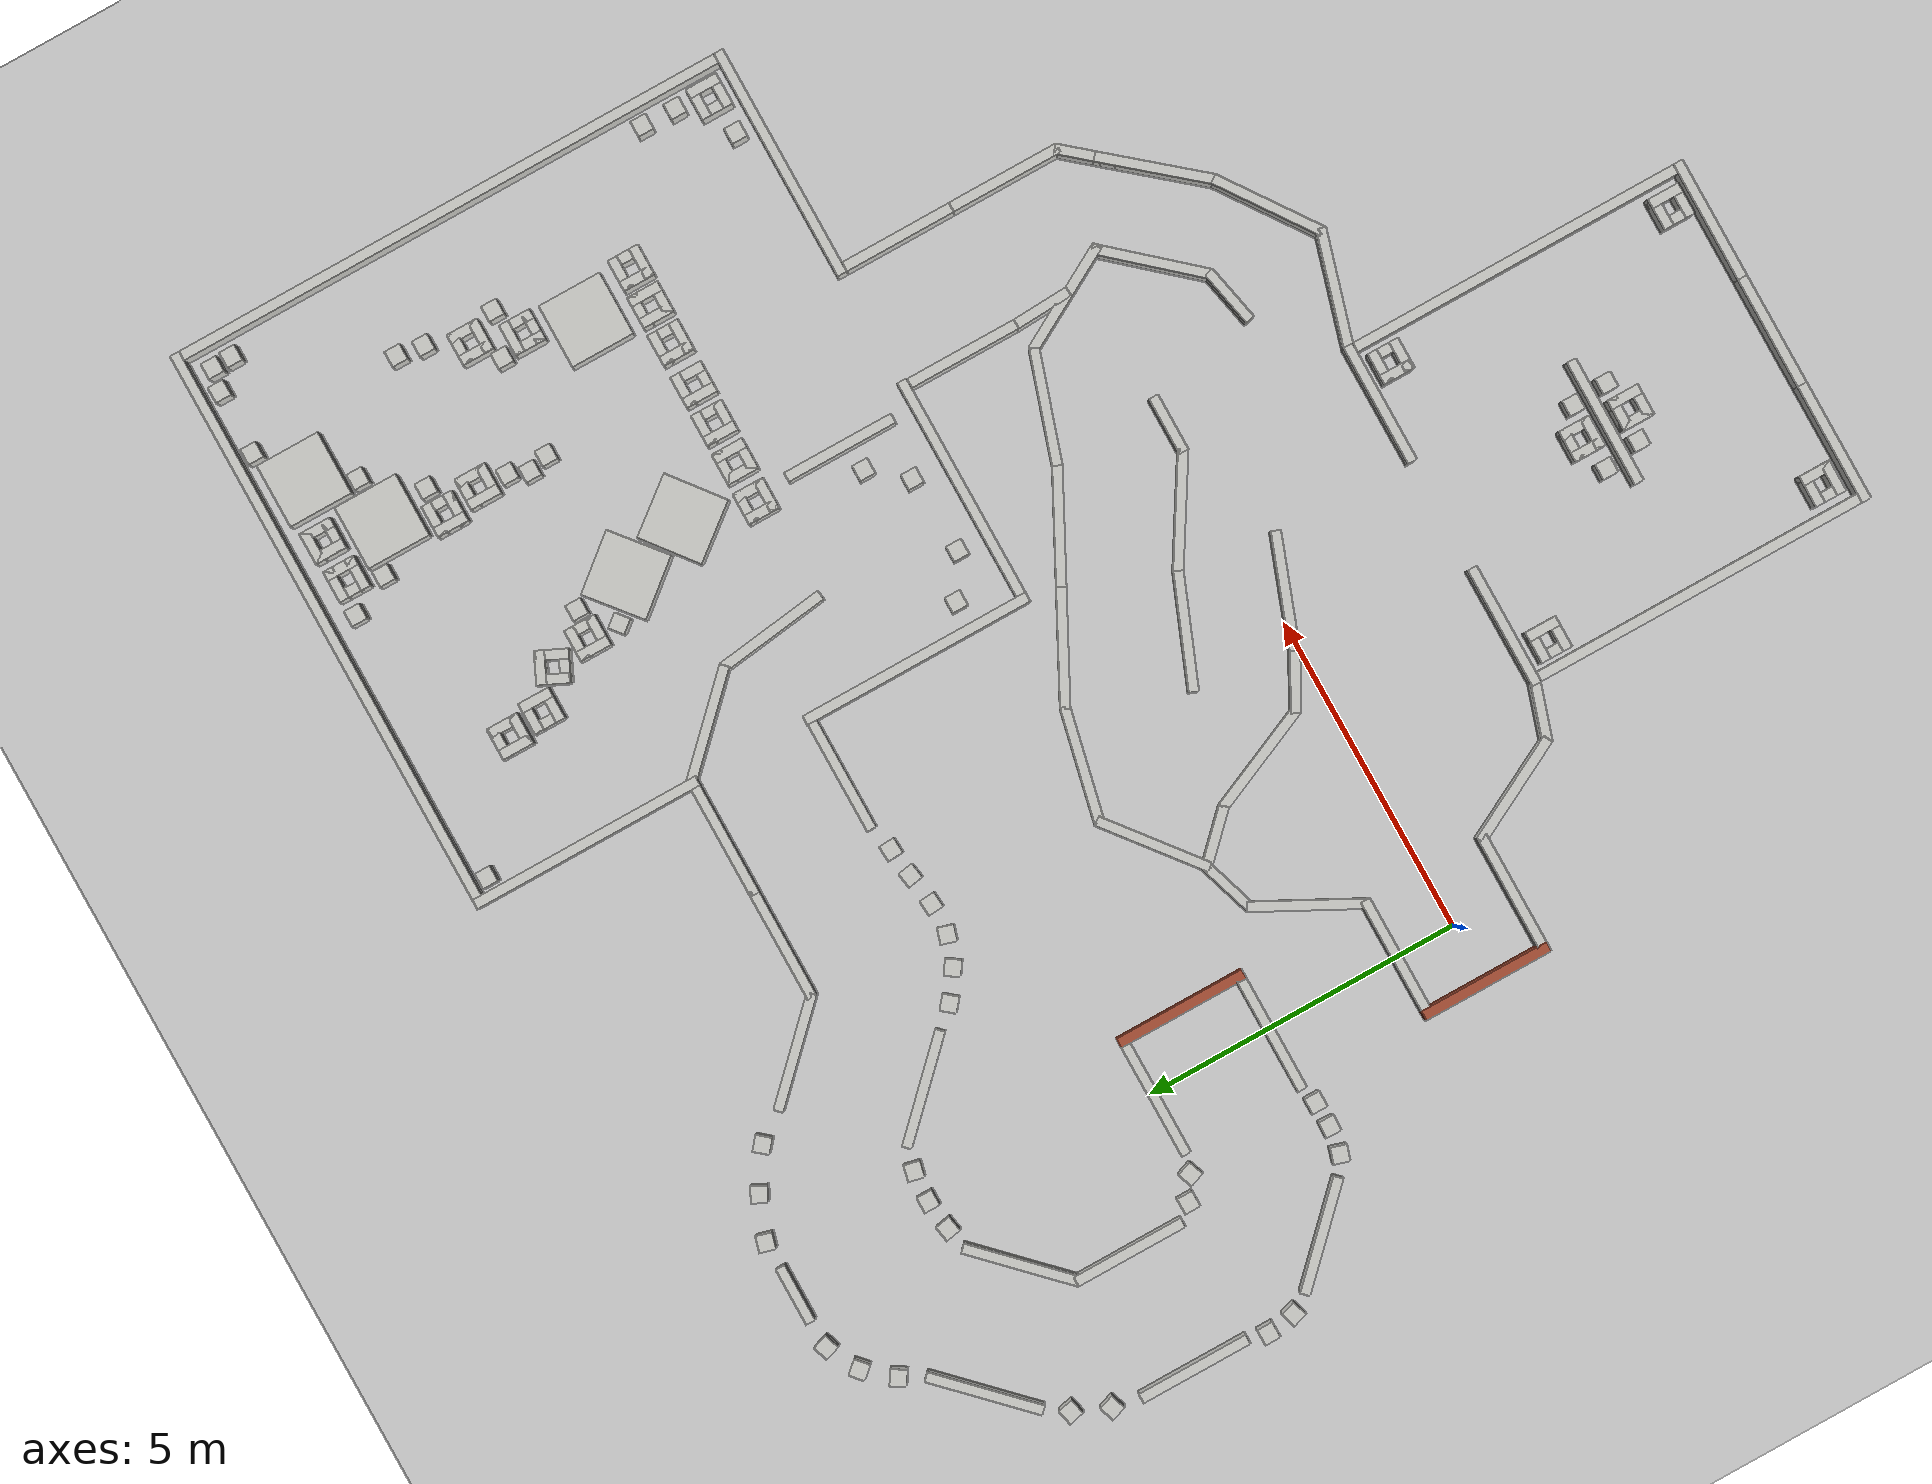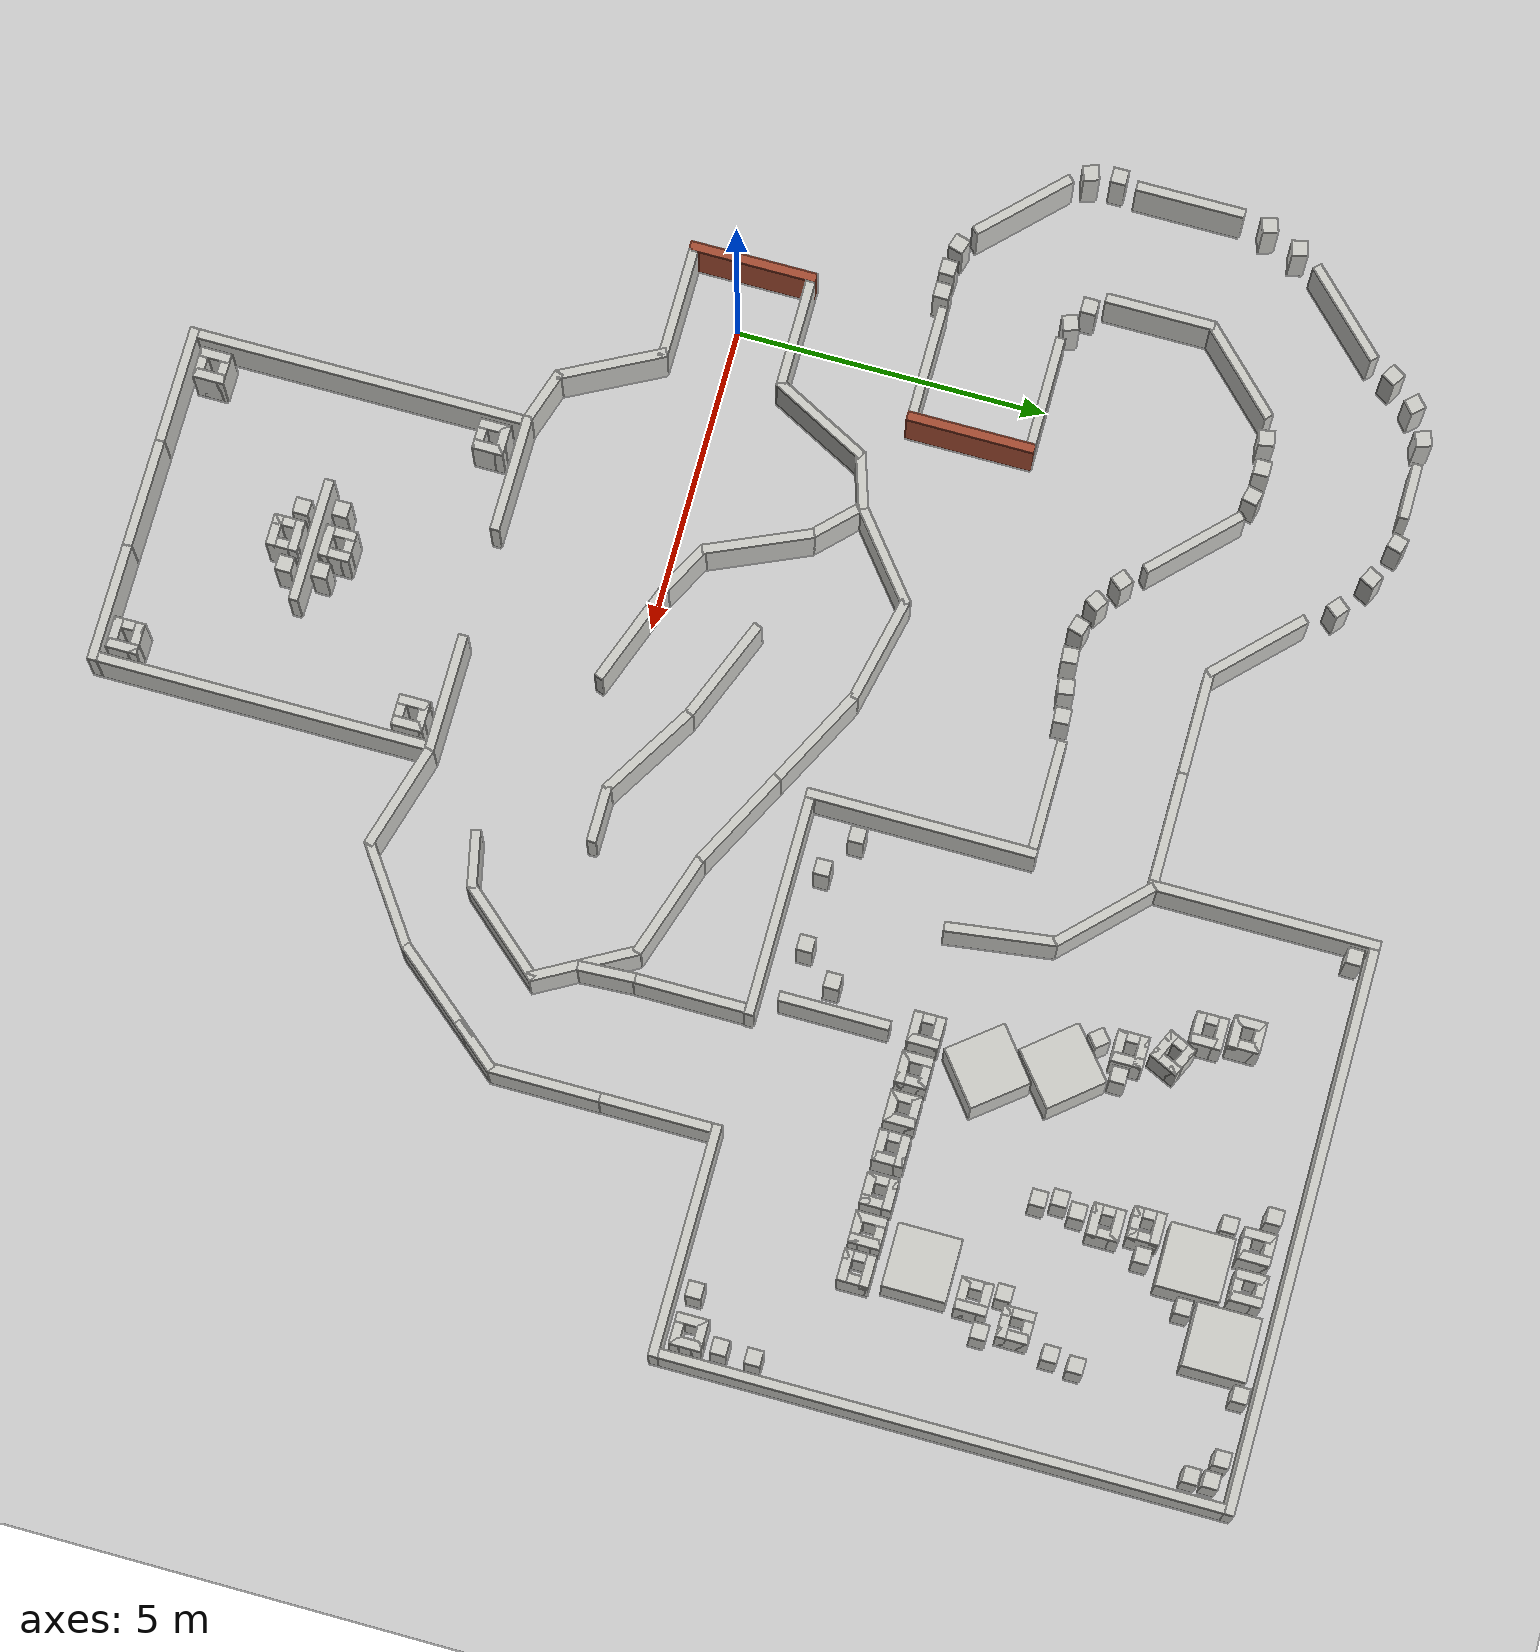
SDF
<sdf version="1.6">
 <world name="default">
  <light name="sun" type="directional">
   <pose>0 0 10 0 -0 0</pose>
   <diffuse>0.8 0.8 0.8 1</diffuse>
   <specular>0.1 0.1 0.1 1</specular>
   <attenuation>
    <range>1000</range>
    <constant>0.9</constant>
    <linear>0.01</linear>
    <quadratic>0.001</quadratic>
   </attenuation>
   <direction>-0.5 0.5 -1</direction>
  </light>
  <model name="ground_plane">
   <static>1</static>
   <link name="link">
    <collision name="collision">
     <geometry><plane><normal>0 0 1</normal><size>100 100</size></plane></geometry>
     <surface><friction><ode><mu>100</mu><mu2>50</mu2></ode></friction></surface>
    </collision>
    <visual name="visual">
     <cast_shadows>0</cast_shadows>
     <geometry><plane><normal>0 0 1</normal><size>100 100</size></plane></geometry>
     <material>
      <script><uri>file://media/materials/scripts/concrete.material</uri><name>Concrete/1</name></script>
     </material>
    </visual>
   </link>
  </model>
  <gravity>0 0 -9.8</gravity>
  <magnetic_field>6e-06 2.3e-05 -4.2e-05</magnetic_field>
  <atmosphere type="adiabatic"/>
  <physics name="default_physics" default="0" type="ode">
   <max_step_size>0.001</max_step_size>
   <real_time_factor>1</real_time_factor>
   <real_time_update_rate>1000</real_time_update_rate>
  </physics>
  <scene><ambient>0.4 0.4 0.4 1</ambient><background>0.7 0.7 0.7 1</background><shadows>1</shadows></scene>
  <spherical_coordinates>
   <surface_model>EARTH_WGS84</surface_model>
   <latitude_deg>0</latitude_deg>
   <longitude_deg>0</longitude_deg>
   <elevation>0</elevation>
   <heading_deg>0</heading_deg>
  </spherical_coordinates>
  <model name="track_end">
   <static>1</static>
   <pose>0 0 0 0 -0 1.5708</pose>
   <link name="Wall_1">
    <collision name="Wall_1_Collision">
     <geometry><box><size>1.8 0.15 1</size></box></geometry>
     <pose>0 0 0.5 0 -0 0</pose>
    </collision>
    <visual name="Wall_1_Visual">
     <pose>0 0 0.5 0 -0 0</pose>
     <geometry><box><size>1.8 0.15 1</size></box></geometry>
     <material>
      <script><uri>file://media/materials/scripts/gazebo.material</uri><name>Gazebo/CeilingTiled</name></script>
      <ambient>1 0.764706 0.305882 1</ambient>
     </material>
    </visual>
    <pose>-0.95 -0.065 0 0 0 -1.5708</pose>
   </link>
   <link name="Wall_2">
    <collision name="Wall_2_Collision">
     <geometry><box><size>1.8 0.15 1</size></box></geometry>
     <pose>0 0 0.5 0 -0 0</pose>
    </collision>
    <visual name="Wall_2_Visual">
     <pose>0 0 0.5 0 -0 0</pose>
     <geometry><box><size>1.8 0.15 1</size></box></geometry>
     <material>
      <script><uri>file://media/materials/scripts/gazebo.material</uri><name>Gazebo/CeilingTiled</name></script>
      <ambient>1 0.764706 0.305882 1</ambient>
     </material>
    </visual>
    <pose>0.95 -0.065 0 0 0 -1.5708</pose>
   </link>
   <link name="Wall_3">
    <collision name="Wall_3_Collision">
     <geometry><box><size>2.05 0.15 1.5</size></box></geometry>
     <pose>0 0 0.75 0 -0 0</pose>
    </collision>
    <visual name="Wall_3_Visual">
     <pose>0 0 0.5 0 -0 0</pose>
     <geometry><box><size>2.05 0.15 1</size></box></geometry>
     <material>
      <script><uri>file://media/materials/scripts/gazebo.material</uri><name>Gazebo/Bricks</name></script>
      <ambient>0.996078 0.47451 0.0196078 1</ambient>
     </material>
    </visual>
    <pose>0 0.89 0 0 -0 0</pose>
   </link>
  </model>
  <model name="obstacle_wall_full">
   <static>1</static>
   <pose>1.3045 -1.68499 0 0 0 -1.08983</pose>
   <link name="Wall">
    <collision name="Wall_Collision">
     <geometry><box><size>1.75 0.15 1</size></box></geometry>
     <pose>0 0 0.5 0 -0 0</pose>
    </collision>
    <visual name="Wall_Visual">
     <pose>0 0 0.5 0 -0 0</pose>
     <geometry><box><size>1.75 0.15 1</size></box></geometry>
     <material>
      <script><uri>file://media/materials/scripts/gazebo.material</uri><name>Gazebo/CeilingTiled</name></script>
      <ambient>1 0.764706 0.305882 1</ambient>
     </material>
    </visual>
   </link>
  </model>
  <model name="obstacle_wall_full_clone">
   <static>1</static>
   <pose>1.30409 1.69422 0 0 -0 1.08983</pose>
   <link name="Wall">
    <collision name="Wall_Collision">
     <geometry><box><size>1.75 0.15 1</size></box></geometry>
     <pose>0 0 0.5 0 -0 0</pose>
    </collision>
    <visual name="Wall_Visual">
     <pose>0 0 0.5 0 -0 0</pose>
     <geometry><box><size>1.75 0.15 1</size></box></geometry>
     <material>
      <script><uri>file://media/materials/scripts/gazebo.material</uri><name>Gazebo/CeilingTiled</name></script>
      <ambient>1 0.764706 0.305882 1</ambient>
     </material>
    </visual>
   </link>
  </model>
  <model name="obstacle_wall_short">
   <static>1</static>
   <pose>2.09444 -2.56147 0 0 0 -0.312022</pose>
   <link name="Wall">
    <collision name="Wall_Collision">
     <geometry><box><size>0.9 0.15 1</size></box></geometry>
     <pose>0 0 0.5 0 -0 0</pose>
    </collision>
    <visual name="Wall_Visual">
     <pose>0 0 0.5 0 -0 0</pose>
     <geometry><box><size>0.9 0.15 1</size></box></geometry>
     <material>
      <script><uri>file://media/materials/scripts/gazebo.material</uri><name>Gazebo/CeilingTiled</name></script>
      <ambient>1 0.764706 0.305882 1</ambient>
     </material>
    </visual>
   </link>
  </model>
  <model name="obstacle_wall_short_clone">
   <static>1</static>
   <pose>2.09475 2.57016 0 0 -0 0.312022</pose>
   <link name="Wall">
    <collision name="Wall_Collision">
     <geometry><box><size>0.9 0.15 1</size></box></geometry>
     <pose>0 0 0.5 0 -0 0</pose>
    </collision>
    <visual name="Wall_Visual">
     <pose>0 0 0.5 0 -0 0</pose>
     <geometry><box><size>0.9 0.15 1</size></box></geometry>
     <material>
      <script><uri>file://media/materials/scripts/gazebo.material</uri><name>Gazebo/CeilingTiled</name></script>
      <ambient>1 0.764706 0.305882 1</ambient>
     </material>
    </visual>
   </link>
  </model>
  <model name="obstacle_wall_full_1">
   <static>1</static>
   <pose>5.57374 1.31756 0 0 0 -0.381039</pose>
   <link name="Wall">
    <collision name="Wall_Collision">
     <geometry><box><size>1.75 0.15 1</size></box></geometry>
     <pose>0 0 0.5 0 -0 0</pose>
    </collision>
    <visual name="Wall_Visual">
     <pose>0 0 0.5 0 -0 0</pose>
     <geometry><box><size>1.75 0.15 1</size></box></geometry>
     <material>
      <script><uri>file://media/materials/scripts/gazebo.material</uri><name>Gazebo/CeilingTiled</name></script>
      <ambient>1 0.764706 0.305882 1</ambient>
     </material>
    </visual>
   </link>
  </model>
  <model name="obstacle_wall_full_2">
   <static>1</static>
   <pose>3.14271 3.20394 0 0 -0 0.673556</pose>
   <link name="Wall">
    <collision name="Wall_Collision">
     <geometry><box><size>1.75 0.15 1</size></box></geometry>
     <pose>0 0 0.5 0 -0 0</pose>
    </collision>
    <visual name="Wall_Visual">
     <pose>0 0 0.5 0 -0 0</pose>
     <geometry><box><size>1.75 0.15 1</size></box></geometry>
     <material>
      <script><uri>file://media/materials/scripts/gazebo.material</uri><name>Gazebo/CeilingTiled</name></script>
      <ambient>1 0.764706 0.305882 1</ambient>
     </material>
    </visual>
   </link>
  </model>
  <model name="obstacle_wall_short_0">
   <static>1</static>
   <pose>2.80877 2.37167 0 0 0 -0.784312</pose>
   <link name="Wall">
    <collision name="Wall_Collision">
     <geometry><box><size>0.9 0.15 1</size></box></geometry>
     <pose>0 0 0.5 0 -0 0</pose>
    </collision>
    <visual name="Wall_Visual">
     <pose>0 0 0.5 0 -0 0</pose>
     <geometry><box><size>0.9 0.15 1</size></box></geometry>
     <material>
      <script><uri>file://media/materials/scripts/gazebo.material</uri><name>Gazebo/CeilingTiled</name></script>
      <ambient>1 0.764706 0.305882 1</ambient>
     </material>
    </visual>
   </link>
  </model>
  <model name="obstacle_wall_full_3">
   <static>1</static>
   <pose>4.62017 3.54539 0 0 0 -0.217442</pose>
   <link name="Wall">
    <collision name="Wall_Collision">
     <geometry><box><size>1.75 0.15 1</size></box></geometry>
     <pose>0 0 0.5 0 -0 0</pose>
    </collision>
    <visual name="Wall_Visual">
     <pose>0 0 0.5 0 -0 0</pose>
     <geometry><box><size>1.75 0.15 1</size></box></geometry>
     <material>
      <script><uri>file://media/materials/scripts/gazebo.material</uri><name>Gazebo/CeilingTiled</name></script>
      <ambient>1 0.764706 0.305882 1</ambient>
     </material>
    </visual>
   </link>
  </model>
  <model name="obstacle_wall_full_3_clone">
   <static>1</static>
   <pose>6.22651 2.96567 0 0 0 -0.475423</pose>
   <link name="Wall">
    <collision name="Wall_Collision">
     <geometry><box><size>1.75 0.15 1</size></box></geometry>
     <pose>0 0 0.5 0 -0 0</pose>
    </collision>
    <visual name="Wall_Visual">
     <pose>0 0 0.5 0 -0 0</pose>
     <geometry><box><size>1.75 0.15 1</size></box></geometry>
     <material>
      <script><uri>file://media/materials/scripts/gazebo.material</uri><name>Gazebo/CeilingTiled</name></script>
      <ambient>1 0.764706 0.305882 1</ambient>
     </material>
    </visual>
   </link>
  </model>
  <model name="obstacle_wall_full_3_clone_0">
   <static>1</static>
   <pose>9.37232 1.50284 0 0 0 -0.313905</pose>
   <link name="Wall">
    <collision name="Wall_Collision">
     <geometry><box><size>1.75 0.15 1</size></box></geometry>
     <pose>0 0 0.5 0 -0 0</pose>
    </collision>
    <visual name="Wall_Visual">
     <pose>0 0 0.5 0 -0 0</pose>
     <geometry><box><size>1.75 0.15 1</size></box></geometry>
     <material>
      <script><uri>file://media/materials/scripts/gazebo.material</uri><name>Gazebo/CeilingTiled</name></script>
      <ambient>1 0.764706 0.305882 1</ambient>
     </material>
    </visual>
   </link>
  </model>
  <model name="obstacle_wall_full_1_clone">
   <static>1</static>
   <pose>5.39001 -0.205171 0 0 0 -0.350489</pose>
   <link name="Wall">
    <collision name="Wall_Collision">
     <geometry><box><size>1.75 0.15 1</size></box></geometry>
     <pose>0 0 0.5 0 -0 0</pose>
    </collision>
    <visual name="Wall_Visual">
     <pose>0 0 0.5 0 -0 0</pose>
     <geometry><box><size>1.75 0.15 1</size></box></geometry>
     <material>
      <script><uri>file://media/materials/scripts/gazebo.material</uri><name>Gazebo/CeilingTiled</name></script>
      <ambient>1 0.764706 0.305882 1</ambient>
     </material>
    </visual>
   </link>
  </model>
  <model name="obstacle_wall_full_1_clone_clone">
   <static>1</static>
   <pose>3.46437 1.27793 0 0 0 -1.15469</pose>
   <link name="Wall">
    <collision name="Wall_Collision">
     <geometry><box><size>1.75 0.15 1</size></box></geometry>
     <pose>0 0 0.5 0 -0 0</pose>
    </collision>
    <visual name="Wall_Visual">
     <pose>0 0 0.5 0 -0 0</pose>
     <geometry><box><size>1.75 0.15 1</size></box></geometry>
     <material>
      <script><uri>file://media/materials/scripts/gazebo.material</uri><name>Gazebo/CeilingTiled</name></script>
      <ambient>1 0.764706 0.305882 1</ambient>
     </material>
    </visual>
   </link>
  </model>
  <model name="obstacle_wall_full_1_clone_0">
   <static>1</static>
   <pose>7.12219 0.54276 0 0 0 -0.548597</pose>
   <link name="Wall">
    <collision name="Wall_Collision">
     <geometry><box><size>1.75 0.15 1</size></box></geometry>
     <pose>0 0 0.5 0 -0 0</pose>
    </collision>
    <visual name="Wall_Visual">
     <pose>0 0 0.5 0 -0 0</pose>
     <geometry><box><size>1.75 0.15 1</size></box></geometry>
     <material>
      <script><uri>file://media/materials/scripts/gazebo.material</uri><name>Gazebo/CeilingTiled</name></script>
      <ambient>1 0.764706 0.305882 1</ambient>
     </material>
    </visual>
   </link>
  </model>
  <model name="obstacle_wall_full_1_clone_clone_0">
   <static>1</static>
   <pose>8.83537 -2.93365 0 0 0 -0.280347</pose>
   <link name="Wall">
    <collision name="Wall_Collision">
     <geometry><box><size>1.75 0.15 1</size></box></geometry>
     <pose>0 0 0.5 0 -0 0</pose>
    </collision>
    <visual name="Wall_Visual">
     <pose>0 0 0.5 0 -0 0</pose>
     <geometry><box><size>1.75 0.15 1</size></box></geometry>
     <material>
      <script><uri>file://media/materials/scripts/gazebo.material</uri><name>Gazebo/CeilingTiled</name></script>
      <ambient>1 0.764706 0.305882 1</ambient>
     </material>
    </visual>
   </link>
  </model>
  <model name="obstacle_wall_full_1_clone_clone_1">
   <static>1</static>
   <pose>10.3251 -2.68236 0 0 -0 0.614772</pose>
   <link name="Wall">
    <collision name="Wall_Collision">
     <geometry><box><size>1.75 0.15 1</size></box></geometry>
     <pose>0 0 0.5 0 -0 0</pose>
    </collision>
    <visual name="Wall_Visual">
     <pose>0 0 0.5 0 -0 0</pose>
     <geometry><box><size>1.75 0.15 1</size></box></geometry>
     <material>
      <script><uri>file://media/materials/scripts/gazebo.material</uri><name>Gazebo/CeilingTiled</name></script>
      <ambient>1 0.764706 0.305882 1</ambient>
     </material>
    </visual>
   </link>
  </model>
  <model name="obstacle_wall_short_1">
   <static>1</static>
   <pose>4.18297 0.301276 0 0 0 -0.489846</pose>
   <link name="Wall">
    <collision name="Wall_Collision">
     <geometry><box><size>0.9 0.15 1</size></box></geometry>
     <pose>0 0 0.5 0 -0 0</pose>
    </collision>
    <visual name="Wall_Visual">
     <pose>0 0 0.5 0 -0 0</pose>
     <geometry><box><size>0.9 0.15 1</size></box></geometry>
     <material>
      <script><uri>file://media/materials/scripts/gazebo.material</uri><name>Gazebo/CeilingTiled</name></script>
      <ambient>1 0.764706 0.305882 1</ambient>
     </material>
    </visual>
   </link>
  </model>
  <model name="obstacle_wall_full_4">
   <static>1</static>
   <pose>10.4365 -0.832267 0 0 0 -2.28923</pose>
   <link name="Wall">
    <collision name="Wall_Collision">
     <geometry><box><size>1.75 0.15 1</size></box></geometry>
     <pose>0 0 0.5 0 -0 0</pose>
    </collision>
    <visual name="Wall_Visual">
     <pose>0 0 0.5 0 -0 0</pose>
     <geometry><box><size>1.75 0.15 1</size></box></geometry>
     <material>
      <script><uri>file://media/materials/scripts/gazebo.material</uri><name>Gazebo/CeilingTiled</name></script>
      <ambient>1 0.764706 0.305882 1</ambient>
     </material>
    </visual>
   </link>
  </model>
  <model name="obstacle_wall_full_3_clone_clone">
   <static>1</static>
   <pose>7.77548 2.16764 0 0 0 -0.475423</pose>
   <link name="Wall">
    <collision name="Wall_Collision">
     <geometry><box><size>1.75 0.15 1</size></box></geometry>
     <pose>0 0 0.5 0 -0 0</pose>
    </collision>
    <visual name="Wall_Visual">
     <pose>0 0 0.5 0 -0 0</pose>
     <geometry><box><size>1.75 0.15 1</size></box></geometry>
     <material>
      <script><uri>file://media/materials/scripts/gazebo.material</uri><name>Gazebo/CeilingTiled</name></script>
      <ambient>1 0.764706 0.305882 1</ambient>
     </material>
    </visual>
   </link>
  </model>
  <model name="room_3x3_split">
   <static>1</static>
   <pose>5.24355 -5.39607 0 0 -0 0</pose>
   <link name="Wall_1">
    <collision name="Wall_1_Collision">
     <geometry><box><size>5.25 0.15 1</size></box></geometry>
     <pose>0 0 0.5 0 -0 0</pose>
    </collision>
    <visual name="Wall_1_Visual">
     <pose>0 0 0.5 0 -0 0</pose>
     <geometry><box><size>5.25 0.15 1</size></box></geometry>
     <material>
      <script><uri>file://media/materials/scripts/gazebo.material</uri><name>Gazebo/CeilingTiled</name></script>
      <ambient>1 0.764706 0.305882 1</ambient>
     </material>
    </visual>
    <pose>-2.69653 -0.003278 0 0 0 -1.5708</pose>
   </link>
   <link name="Wall_2">
    <collision name="Wall_2_Collision">
     <geometry><box><size>5.25 0.15 1</size></box></geometry>
     <pose>0 0 0.5 0 -0 0</pose>
    </collision>
    <visual name="Wall_2_Visual">
     <pose>0 0 0.5 0 -0 0</pose>
     <geometry><box><size>5.25 0.15 1</size></box></geometry>
     <material>
      <script><uri>file://media/materials/scripts/gazebo.material</uri><name>Gazebo/CeilingTiled</name></script>
      <ambient>1 0.764706 0.305882 1</ambient>
     </material>
    </visual>
    <pose>2.69688 -0.000452 0 0 0 -1.5708</pose>
   </link>
   <link name="Wall_3">
    <collision name="Wall_3_Collision">
     <geometry><box><size>1.9 0.15 1</size></box></geometry>
     <pose>0 0 0.5 0 -0 0</pose>
    </collision>
    <visual name="Wall_3_Visual">
     <pose>0 0 0.5 0 -0 0</pose>
     <geometry><box><size>1.9 0.15 1</size></box></geometry>
     <material>
      <script><uri>file://media/materials/scripts/gazebo.material</uri><name>Gazebo/CeilingTiled</name></script>
      <ambient>1 0.764706 0.305882 1</ambient>
     </material>
    </visual>
    <pose>-1.82279 -2.70217 0 0 -0 0</pose>
   </link>
   <link name="Wall_4">
    <collision name="Wall_4_Collision">
     <geometry><box><size>1.9 0.15 1</size></box></geometry>
     <pose>0 0 0.5 0 -0 0</pose>
    </collision>
    <visual name="Wall_4_Visual">
     <pose>0 0 0.5 0 -0 0</pose>
     <geometry><box><size>1.9 0.15 1</size></box></geometry>
     <material>
      <script><uri>file://media/materials/scripts/gazebo.material</uri><name>Gazebo/CeilingTiled</name></script>
      <ambient>1 0.764706 0.305882 1</ambient>
     </material>
    </visual>
    <pose>-1.82219 2.69878 0 0 -0 0</pose>
   </link>
   <link name="Wall_5">
    <collision name="Wall_5_Collision">
     <geometry><box><size>1.9 0.15 1</size></box></geometry>
     <pose>0 0 0.5 0 -0 0</pose>
    </collision>
    <visual name="Wall_5_Visual">
     <pose>0 0 0.5 0 -0 0</pose>
     <geometry><box><size>1.9 0.15 1</size></box></geometry>
     <material>
      <script><uri>file://media/materials/scripts/gazebo.material</uri><name>Gazebo/CeilingTiled</name></script>
      <ambient>1 0.764706 0.305882 1</ambient>
     </material>
    </visual>
    <pose>1.82194 2.70217 0 0 -0 0</pose>
   </link>
   <link name="Wall_6">
    <collision name="Wall_6_Collision">
     <geometry><box><size>1.9 0.15 1</size></box></geometry>
     <pose>0 0 0.5 0 -0 0</pose>
    </collision>
    <visual name="Wall_6_Visual">
     <pose>0 0 0.5 0 -0 0</pose>
     <geometry><box><size>1.9 0.15 1</size></box></geometry>
     <material>
      <script><uri>file://media/materials/scripts/gazebo.material</uri><name>Gazebo/CeilingTiled</name></script>
      <ambient>1 0.764706 0.305882 1</ambient>
     </material>
    </visual>
    <pose>1.82279 -2.70173 0 0 -0 0</pose>
   </link>
   <link name="Wall_7">
    <collision name="Wall_7_Collision">
     <geometry><box><size>2 0.15 1</size></box></geometry>
     <pose>0 0 0.5 0 -0 0</pose>
    </collision>
    <visual name="Wall_7_Visual">
     <pose>0 0 0.5 0 -0 0</pose>
     <geometry><box><size>2 0.15 1</size></box></geometry>
     <material>
      <script><uri>file://media/materials/scripts/gazebo.material</uri><name>Gazebo/CeilingTiled</name></script>
      <ambient>1 0.764706 0.305882 1</ambient>
     </material>
    </visual>
    <pose>0.033144 0.01482 0 0 -0 0</pose>
   </link>
  </model>
  <model name="obstacle_wall_full_6">
   <static>1</static>
   <pose>5.24644 -8.09756 0 0 -0 0</pose>
   <link name="Wall">
    <collision name="Wall_Collision">
     <geometry><box><size>1.75 0.15 1</size></box></geometry>
     <pose>0 0 0.5 0 -0 0</pose>
    </collision>
    <visual name="Wall_Visual">
     <pose>0 0 0.5 0 -0 0</pose>
     <geometry><box><size>1.75 0.15 1</size></box></geometry>
     <material>
      <script><uri>file://media/materials/scripts/gazebo.material</uri><name>Gazebo/CeilingTiled</name></script>
      <ambient>1 0.764706 0.305882 1</ambient>
     </material>
    </visual>
   </link>
  </model>
  <model name="obstacle_wall_short_3">
   <static>1</static>
   <pose>8.28156 0.092512 0 0 -0 0</pose>
   <link name="Wall">
    <collision name="Wall_Collision">
     <geometry><box><size>0.9 0.15 1</size></box></geometry>
     <pose>0 0 0.5 0 -0 0</pose>
    </collision>
    <visual name="Wall_Visual">
     <pose>0 0 0.5 0 -0 0</pose>
     <geometry><box><size>0.9 0.15 1</size></box></geometry>
     <material>
      <script><uri>file://media/materials/scripts/gazebo.material</uri><name>Gazebo/CeilingTiled</name></script>
      <ambient>1 0.764706 0.305882 1</ambient>
     </material>
    </visual>
   </link>
  </model>
  <model name="obstacle_wall_full_7">
   <static>1</static>
   <pose>10.5839 0.504469 0 0 0 -1.06076</pose>
   <link name="Wall">
    <collision name="Wall_Collision">
     <geometry><box><size>1.75 0.15 1</size></box></geometry>
     <pose>0 0 0.5 0 -0 0</pose>
    </collision>
    <visual name="Wall_Visual">
     <pose>0 0 0.5 0 -0 0</pose>
     <geometry><box><size>1.75 0.15 1</size></box></geometry>
     <material>
      <script><uri>file://media/materials/scripts/gazebo.material</uri><name>Gazebo/CeilingTiled</name></script>
      <ambient>1 0.764706 0.305882 1</ambient>
     </material>
    </visual>
   </link>
  </model>
  <model name="obstacle_wall_short_4">
   <static>1</static>
   <pose>9.46195 -1.56066 0 0 -0 0.208509</pose>
   <link name="Wall">
    <collision name="Wall_Collision">
     <geometry><box><size>0.9 0.15 1</size></box></geometry>
     <pose>0 0 0.5 0 -0 0</pose>
    </collision>
    <visual name="Wall_Visual">
     <pose>0 0 0.5 0 -0 0</pose>
     <geometry><box><size>0.9 0.15 1</size></box></geometry>
     <material>
      <script><uri>file://media/materials/scripts/gazebo.material</uri><name>Gazebo/CeilingTiled</name></script>
      <ambient>1 0.764706 0.305882 1</ambient>
     </material>
    </visual>
   </link>
  </model>
  <model name="obstacle_wall_full_8">
   <static>1</static>
   <pose>11.5895 -1.51746 0 0 -0 0.874719</pose>
   <link name="Wall">
    <collision name="Wall_Collision">
     <geometry><box><size>1.75 0.15 1</size></box></geometry>
     <pose>0 0 0.5 0 -0 0</pose>
    </collision>
    <visual name="Wall_Visual">
     <pose>0 0 0.5 0 -0 0</pose>
     <geometry><box><size>1.75 0.15 1</size></box></geometry>
     <material>
      <script><uri>file://media/materials/scripts/gazebo.material</uri><name>Gazebo/CeilingTiled</name></script>
      <ambient>1 0.764706 0.305882 1</ambient>
     </material>
    </visual>
   </link>
  </model>
  <model name="track_straight">
   <static>1</static>
   <pose>11.5484 2.17193 0 0 -0 0</pose>
   <link name="Wall_1">
    <collision name="Wall_1_Collision">
     <geometry><box><size>1.75 0.15 1</size></box></geometry>
     <pose>0 0 0.5 0 -0 0</pose>
    </collision>
    <visual name="Wall_1_Visual">
     <pose>0 0 0.5 0 -0 0</pose>
     <geometry><box><size>1.75 0.15 1</size></box></geometry>
     <material>
      <script><uri>file://media/materials/scripts/gazebo.material</uri><name>Gazebo/CeilingTiled</name></script>
      <ambient>1 0.764706 0.305882 1</ambient>
     </material>
    </visual>
    <pose>-0.955 0.002 0 0 0 -1.5708</pose>
   </link>
   <link name="Wall_2">
    <collision name="Wall_2_Collision">
     <geometry><box><size>1.75 0.15 1</size></box></geometry>
     <pose>0 0 0.5 0 -0 0</pose>
    </collision>
    <visual name="Wall_2_Visual">
     <pose>0 0 0.5 0 -0 0</pose>
     <geometry><box><size>1.75 0.15 1</size></box></geometry>
     <material>
      <script><uri>file://media/materials/scripts/gazebo.material</uri><name>Gazebo/CeilingTiled</name></script>
      <ambient>1 0.764706 0.305882 1</ambient>
     </material>
    </visual>
    <pose>0.955 0.002 0 0 0 -1.5708</pose>
   </link>
  </model>
  <model name="room_5x5_right">
   <static>1</static>
   <pose>11.5539 7.57729 0 0 -0 0</pose>
   <link name="Wall_1">
    <collision name="Wall_1_Collision">
     <geometry><box><size>8.75 0.15 1</size></box></geometry>
     <pose>0 0 0.5 0 -0 0</pose>
    </collision>
    <visual name="Wall_1_Visual">
     <pose>0 0 0.5 0 -0 0</pose>
     <geometry><box><size>8.75 0.15 1</size></box></geometry>
     <material>
      <script><uri>file://media/materials/scripts/gazebo.material</uri><name>Gazebo/CeilingTiled</name></script>
      <ambient>1 0.764706 0.305882 1</ambient>
     </material>
    </visual>
    <pose>4.44912 -0.000431 0 0 0 -1.5708</pose>
   </link>
   <link name="Wall_2">
    <collision name="Wall_2_Collision">
     <geometry><box><size>3.65 0.15 1</size></box></geometry>
     <pose>0 0 0.5 0 -0 0</pose>
    </collision>
    <visual name="Wall_2_Visual">
     <pose>0 0 0.5 0 -0 0</pose>
     <geometry><box><size>3.65 0.15 1</size></box></geometry>
     <material>
      <script><uri>file://media/materials/scripts/gazebo.material</uri><name>Gazebo/CeilingTiled</name></script>
      <ambient>1 0.764706 0.305882 1</ambient>
     </material>
    </visual>
    <pose>-4.44961 2.70076 0 0 0 -1.5708</pose>
   </link>
   <link name="Wall_3">
    <collision name="Wall_3_Collision">
     <geometry><box><size>3.65 0.15 1</size></box></geometry>
     <pose>0 0 0.5 0 -0 0</pose>
    </collision>
    <visual name="Wall_3_Visual">
     <pose>0 0 0.5 0 -0 0</pose>
     <geometry><box><size>3.65 0.15 1</size></box></geometry>
     <material>
      <script><uri>file://media/materials/scripts/gazebo.material</uri><name>Gazebo/CeilingTiled</name></script>
      <ambient>1 0.764706 0.305882 1</ambient>
     </material>
    </visual>
    <pose>2.69961 -4.45076 0 0 -0 0</pose>
   </link>
   <link name="Wall_4">
    <collision name="Wall_4_Collision">
     <geometry><box><size>8.90028 0.15 1</size></box></geometry>
     <pose>0 0 0.5 0 -0 0</pose>
    </collision>
    <visual name="Wall_4_Visual">
     <pose>0 0 0.5 0 -0 0</pose>
     <geometry><box><size>8.90028 0.15 1</size></box></geometry>
     <material>
      <script><uri>file://media/materials/scripts/gazebo.material</uri><name>Gazebo/CeilingTiled</name></script>
      <ambient>1 0.764706 0.305882 1</ambient>
     </material>
    </visual>
    <pose>0.074346 4.45022 0 0 0 -6.5e-05</pose>
   </link>
   <link name="Wall_5">
    <collision name="Wall_5_Collision">
     <geometry><box><size>3.5 0.15 1</size></box></geometry>
     <pose>0 0 0.5 0 -0 0</pose>
    </collision>
    <visual name="Wall_5_Visual">
     <pose>0 0 0.5 0 -0 0</pose>
     <geometry><box><size>3.5 0.15 1</size></box></geometry>
     <material>
      <script><uri>file://media/materials/scripts/gazebo.material</uri><name>Gazebo/CeilingTiled</name></script>
      <ambient>1 0.764706 0.305882 1</ambient>
     </material>
    </visual>
    <pose>-2.62383 -4.4498 0 0 -0 0</pose>
   </link>
   <link name="Wall_6">
    <collision name="Wall_6_Collision">
     <geometry><box><size>3.65 0.15 1</size></box></geometry>
     <pose>0 0 0.5 0 -0 0</pose>
    </collision>
    <visual name="Wall_6_Visual">
     <pose>0 0 0.5 0 -0 0</pose>
     <geometry><box><size>3.65 0.15 1</size></box></geometry>
     <material>
      <script><uri>file://media/materials/scripts/gazebo.material</uri><name>Gazebo/CeilingTiled</name></script>
      <ambient>1 0.764706 0.305882 1</ambient>
     </material>
    </visual>
    <pose>-4.44941 -2.70044 0 0 0 -1.5708</pose>
   </link>
  </model>
  <model name="obstacle_wall_full_10">
   <static>1</static>
   <pose>12.5056 0.423565 0 0 0 -1.5708</pose>
   <link name="Wall">
    <collision name="Wall_Collision">
     <geometry><box><size>1.75 0.15 1</size></box></geometry>
     <pose>0 0 0.5 0 -0 0</pose>
    </collision>
    <visual name="Wall_Visual">
     <pose>0 0 0.5 0 -0 0</pose>
     <geometry><box><size>1.75 0.15 1</size></box></geometry>
     <material>
      <script><uri>file://media/materials/scripts/gazebo.material</uri><name>Gazebo/CeilingTiled</name></script>
      <ambient>1 0.764706 0.305882 1</ambient>
     </material>
    </visual>
   </link>
  </model>
  <model name="obstacle_wall_short_7">
   <static>1</static>
   <pose>12.2351 -0.745772 0 0 -0 0.872096</pose>
   <link name="Wall">
    <collision name="Wall_Collision">
     <geometry><box><size>0.9 0.15 1</size></box></geometry>
     <pose>0 0 0.5 0 -0 0</pose>
    </collision>
    <visual name="Wall_Visual">
     <pose>0 0 0.5 0 -0 0</pose>
     <geometry><box><size>0.9 0.15 1</size></box></geometry>
     <material>
      <script><uri>file://media/materials/scripts/gazebo.material</uri><name>Gazebo/CeilingTiled</name></script>
      <ambient>1 0.764706 0.305882 1</ambient>
     </material>
    </visual>
   </link>
  </model>
  <model name="obstacle_wall_short_8">
   <static>1</static>
   <pose>10.6141 0.867782 0 0 0 -1.5211</pose>
   <link name="Wall">
    <collision name="Wall_Collision">
     <geometry><box><size>0.9 0.15 1</size></box></geometry>
     <pose>0 0 0.5 0 -0 0</pose>
    </collision>
    <visual name="Wall_Visual">
     <pose>0 0 0.5 0 -0 0</pose>
     <geometry><box><size>0.9 0.15 1</size></box></geometry>
     <material>
      <script><uri>file://media/materials/scripts/gazebo.material</uri><name>Gazebo/CeilingTiled</name></script>
      <ambient>1 0.764706 0.305882 1</ambient>
     </material>
    </visual>
   </link>
  </model>
  <model name="track_straight_0">
   <static>1</static>
   <pose>6.1613 7.57532 0 0 -0 1.5708</pose>
   <link name="Wall_1">
    <collision name="Wall_1_Collision">
     <geometry><box><size>1.75 0.15 1</size></box></geometry>
     <pose>0 0 0.5 0 -0 0</pose>
    </collision>
    <visual name="Wall_1_Visual">
     <pose>0 0 0.5 0 -0 0</pose>
     <geometry><box><size>1.75 0.15 1</size></box></geometry>
     <material>
      <script><uri>file://media/materials/scripts/gazebo.material</uri><name>Gazebo/CeilingTiled</name></script>
      <ambient>1 0.764706 0.305882 1</ambient>
     </material>
    </visual>
    <pose>-0.955 0.002 0 0 0 -1.5708</pose>
   </link>
   <link name="Wall_2">
    <collision name="Wall_2_Collision">
     <geometry><box><size>1.75 0.15 1</size></box></geometry>
     <pose>0 0 0.5 0 -0 0</pose>
    </collision>
    <visual name="Wall_2_Visual">
     <pose>0 0 0.5 0 -0 0</pose>
     <geometry><box><size>1.75 0.15 1</size></box></geometry>
     <material>
      <script><uri>file://media/materials/scripts/gazebo.material</uri><name>Gazebo/CeilingTiled</name></script>
      <ambient>1 0.764706 0.305882 1</ambient>
     </material>
    </visual>
    <pose>0.955 0.002 0 0 0 -1.5708</pose>
   </link>
  </model>
  <model name="track_straight_0_clone_0">
   <static>1</static>
   <pose>-1.86828 8.45595 0 0 -0 2.3562</pose>
   <link name="Wall_1">
    <collision name="Wall_1_Collision">
     <geometry><box><size>1.75 0.15 1</size></box></geometry>
     <pose>0 0 0.5 0 -0 0</pose>
    </collision>
    <visual name="Wall_1_Visual">
     <pose>0 0 0.5 0 -0 0</pose>
     <geometry><box><size>1.75 0.15 1</size></box></geometry>
     <material>
      <script><uri>file://media/materials/scripts/gazebo.material</uri><name>Gazebo/CeilingTiled</name></script>
      <ambient>1 0.764706 0.305882 1</ambient>
     </material>
    </visual>
    <pose>-0.955 0.002 0 0 0 -1.5708</pose>
   </link>
   <link name="Wall_2">
    <collision name="Wall_2_Collision">
     <geometry><box><size>1.75 0.15 1</size></box></geometry>
     <pose>0 0 0.5 0 -0 0</pose>
    </collision>
    <visual name="Wall_2_Visual">
     <pose>0 0 0.5 0 -0 0</pose>
     <geometry><box><size>1.75 0.15 1</size></box></geometry>
     <material>
      <script><uri>file://media/materials/scripts/gazebo.material</uri><name>Gazebo/CeilingTiled</name></script>
      <ambient>1 0.764706 0.305882 1</ambient>
     </material>
    </visual>
    <pose>0.955 0.002 0 0 0 -1.5708</pose>
   </link>
  </model>
  <model name="track_straight_0_clone_1">
   <static>1</static>
   <pose>-2.74466 6.33811 0 0 -0 0</pose>
   <link name="Wall_1">
    <collision name="Wall_1_Collision">
     <geometry><box><size>1.75 0.15 1</size></box></geometry>
     <pose>0 0 0.5 0 -0 0</pose>
    </collision>
    <visual name="Wall_1_Visual">
     <pose>0 0 0.5 0 -0 0</pose>
     <geometry><box><size>1.75 0.15 1</size></box></geometry>
     <material>
      <script><uri>file://media/materials/scripts/gazebo.material</uri><name>Gazebo/CeilingTiled</name></script>
      <ambient>1 0.764706 0.305882 1</ambient>
     </material>
    </visual>
    <pose>-0.955 0.002 0 0 0 -1.5708</pose>
   </link>
   <link name="Wall_2">
    <collision name="Wall_2_Collision">
     <geometry><box><size>1.75 0.15 1</size></box></geometry>
     <pose>0 0 0.5 0 -0 0</pose>
    </collision>
    <visual name="Wall_2_Visual">
     <pose>0 0 0.5 0 -0 0</pose>
     <geometry><box><size>1.75 0.15 1</size></box></geometry>
     <material>
      <script><uri>file://media/materials/scripts/gazebo.material</uri><name>Gazebo/CeilingTiled</name></script>
      <ambient>1 0.764706 0.305882 1</ambient>
     </material>
    </visual>
    <pose>0.955 0.002 0 0 0 -1.5708</pose>
   </link>
  </model>
  <model name="track_straight_0_clone_2">
   <static>1</static>
   <pose>2.36127 8.45219 0 0 -0 0.785402</pose>
   <link name="Wall_1">
    <collision name="Wall_1_Collision">
     <geometry><box><size>1.75 0.15 1</size></box></geometry>
     <pose>0 0 0.5 0 -0 0</pose>
    </collision>
    <visual name="Wall_1_Visual">
     <pose>0 0 0.5 0 -0 0</pose>
     <geometry><box><size>1.75 0.15 1</size></box></geometry>
     <material>
      <script><uri>file://media/materials/scripts/gazebo.material</uri><name>Gazebo/CeilingTiled</name></script>
      <ambient>1 0.764706 0.305882 1</ambient>
     </material>
    </visual>
    <pose>-0.955 0.002 0 0 0 -1.5708</pose>
   </link>
   <link name="Wall_2">
    <collision name="Wall_2_Collision">
     <geometry><box><size>1.75 0.15 1</size></box></geometry>
     <pose>0 0 0.5 0 -0 0</pose>
    </collision>
    <visual name="Wall_2_Visual">
     <pose>0 0 0.5 0 -0 0</pose>
     <geometry><box><size>1.75 0.15 1</size></box></geometry>
     <material>
      <script><uri>file://media/materials/scripts/gazebo.material</uri><name>Gazebo/CeilingTiled</name></script>
      <ambient>1 0.764706 0.305882 1</ambient>
     </material>
    </visual>
    <pose>0.955 0.002 0 0 0 -1.5708</pose>
   </link>
  </model>
  <model name="obstacle_wall_short_9">
   <static>1</static>
   <pose>0 10.81 0 0 -0 0</pose>
   <link name="Wall">
    <collision name="Wall_Collision">
     <geometry><box><size>0.9 0.15 1</size></box></geometry>
     <pose>0 0 0.5 0 -0 0</pose>
    </collision>
    <visual name="Wall_Visual">
     <pose>0 0 0.5 0 -0 0</pose>
     <geometry><box><size>0.9 0.15 1</size></box></geometry>
     <material>
      <script><uri>file://media/materials/scripts/gazebo.material</uri><name>Gazebo/CeilingTiled</name></script>
      <ambient>1 0.764706 0.305882 1</ambient>
     </material>
    </visual>
   </link>
  </model>
  <model name="obstacle_squarepillar_small">
   <static>1</static>
   <pose>2.10974 10.1788 0 0 -0 0.872076</pose>
   <link name="Pillar">
    <collision name="Pillar_Collision">
     <geometry><box><size>0.25 0.25 1</size></box></geometry>
     <pose>0 0 0.5 0 -0 0</pose>
    </collision>
    <visual name="Pillar_Visual">
     <pose>0 0 0.5 0 -0 0</pose>
     <geometry><box><size>0.25 0.25 1</size></box></geometry>
     <material>
      <script><uri>file://media/materials/scripts/gazebo.material</uri><name>Gazebo/CeilingTiled</name></script>
      <ambient>1 0.764706 0.305882 1</ambient>
     </material>
    </visual>
   </link>
  </model>
  <model name="obstacle_squarepillar_small_clone">
   <static>1</static>
   <pose>1.5116 10.5659 0 0 0 -0.470925</pose>
   <link name="Pillar">
    <collision name="Pillar_Collision">
     <geometry><box><size>0.25 0.25 1</size></box></geometry>
     <pose>0 0 0.5 0 -0 0</pose>
    </collision>
    <visual name="Pillar_Visual">
     <pose>0 0 0.5 0 -0 0</pose>
     <geometry><box><size>0.25 0.25 1</size></box></geometry>
     <material>
      <script><uri>file://media/materials/scripts/gazebo.material</uri><name>Gazebo/CeilingTiled</name></script>
      <ambient>1 0.764706 0.305882 1</ambient>
     </material>
    </visual>
   </link>
  </model>
  <model name="obstacle_squarepillar_small_clone_0">
   <static>1</static>
   <pose>0.86381 10.8205 0 0 0 -0.269082</pose>
   <link name="Pillar">
    <collision name="Pillar_Collision">
     <geometry><box><size>0.25 0.25 1</size></box></geometry>
     <pose>0 0 0.5 0 -0 0</pose>
    </collision>
    <visual name="Pillar_Visual">
     <pose>0 0 0.5 0 -0 0</pose>
     <geometry><box><size>0.25 0.25 1</size></box></geometry>
     <material>
      <script><uri>file://media/materials/scripts/gazebo.material</uri><name>Gazebo/CeilingTiled</name></script>
      <ambient>1 0.764706 0.305882 1</ambient>
     </material>
    </visual>
   </link>
  </model>
  <model name="obstacle_squarepillar_small_clone_1">
   <static>1</static>
   <pose>-1.74834 10.1009 0 0 0 -0.568659</pose>
   <link name="Pillar">
    <collision name="Pillar_Collision">
     <geometry><box><size>0.25 0.25 1</size></box></geometry>
     <pose>0 0 0.5 0 -0 0</pose>
    </collision>
    <visual name="Pillar_Visual">
     <pose>0 0 0.5 0 -0 0</pose>
     <geometry><box><size>0.25 0.25 1</size></box></geometry>
     <material>
      <script><uri>file://media/materials/scripts/gazebo.material</uri><name>Gazebo/CeilingTiled</name></script>
      <ambient>1 0.764706 0.305882 1</ambient>
     </material>
    </visual>
   </link>
  </model>
  <model name="obstacle_squarepillar_small_clone_2">
   <static>1</static>
   <pose>-1.37986 10.5313 0 0 -0 0.724923</pose>
   <link name="Pillar">
    <collision name="Pillar_Collision">
     <geometry><box><size>0.25 0.25 1</size></box></geometry>
     <pose>0 0 0.5 0 -0 0</pose>
    </collision>
    <visual name="Pillar_Visual">
     <pose>0 0 0.5 0 -0 0</pose>
     <geometry><box><size>0.25 0.25 1</size></box></geometry>
     <material>
      <script><uri>file://media/materials/scripts/gazebo.material</uri><name>Gazebo/CeilingTiled</name></script>
      <ambient>1 0.764706 0.305882 1</ambient>
     </material>
    </visual>
   </link>
  </model>
  <model name="obstacle_squarepillar_small_clone_3">
   <static>1</static>
   <pose>-0.873681 10.7903 0 0 -0 0.325172</pose>
   <link name="Pillar">
    <collision name="Pillar_Collision">
     <geometry><box><size>0.25 0.25 1</size></box></geometry>
     <pose>0 0 0.5 0 -0 0</pose>
    </collision>
    <visual name="Pillar_Visual">
     <pose>0 0 0.5 0 -0 0</pose>
     <geometry><box><size>0.25 0.25 1</size></box></geometry>
     <material>
      <script><uri>file://media/materials/scripts/gazebo.material</uri><name>Gazebo/CeilingTiled</name></script>
      <ambient>1 0.764706 0.305882 1</ambient>
     </material>
    </visual>
   </link>
  </model>
  <model name="track_end_0">
   <static>1</static>
   <pose>1e-06 4 0 0 0 -1.57079</pose>
   <link name="Wall_1">
    <collision name="Wall_1_Collision">
     <geometry><box><size>1.8 0.15 1</size></box></geometry>
     <pose>0 0 0.5 0 -0 0</pose>
    </collision>
    <visual name="Wall_1_Visual">
     <pose>0 0 0.5 0 -0 0</pose>
     <geometry><box><size>1.8 0.15 1</size></box></geometry>
     <material>
      <script><uri>file://media/materials/scripts/gazebo.material</uri><name>Gazebo/CeilingTiled</name></script>
      <ambient>1 0.764706 0.305882 1</ambient>
     </material>
    </visual>
    <pose>-0.95 -0.065 0 0 0 -1.5708</pose>
   </link>
   <link name="Wall_2">
    <collision name="Wall_2_Collision">
     <geometry><box><size>1.8 0.15 1</size></box></geometry>
     <pose>0 0 0.5 0 -0 0</pose>
    </collision>
    <visual name="Wall_2_Visual">
     <pose>0 0 0.5 0 -0 0</pose>
     <geometry><box><size>1.8 0.15 1</size></box></geometry>
     <material>
      <script><uri>file://media/materials/scripts/gazebo.material</uri><name>Gazebo/CeilingTiled</name></script>
      <ambient>1 0.764706 0.305882 1</ambient>
     </material>
    </visual>
    <pose>0.95 -0.065 0 0 0 -1.5708</pose>
   </link>
   <link name="Wall_3">
    <collision name="Wall_3_Collision">
     <geometry><box><size>2.05 0.15 1.5</size></box></geometry>
     <pose>0 0 0.75 0 -0 0</pose>
    </collision>
    <visual name="Wall_3_Visual">
     <pose>0 0 0.5 0 -0 0</pose>
     <geometry><box><size>2.05 0.15 1</size></box></geometry>
     <material>
      <script><uri>file://media/materials/scripts/gazebo.material</uri><name>Gazebo/Bricks</name></script>
      <ambient>0.996078 0.47451 0.0196078 1</ambient>
     </material>
    </visual>
    <pose>0 0.89 0 0 -0 0</pose>
   </link>
  </model>
  <model name="obstacle_squarepillar_small_0">
   <static>1</static>
   <pose>0.721248 8.46998 0 0 0 -0.217104</pose>
   <link name="Pillar">
    <collision name="Pillar_Collision">
     <geometry><box><size>0.25 0.25 1</size></box></geometry>
     <pose>0 0 0.5 0 -0 0</pose>
    </collision>
    <visual name="Pillar_Visual">
     <pose>0 0 0.5 0 -0 0</pose>
     <geometry><box><size>0.25 0.25 1</size></box></geometry>
     <material>
      <script><uri>file://media/materials/scripts/gazebo.material</uri><name>Gazebo/CeilingTiled</name></script>
      <ambient>1 0.764706 0.305882 1</ambient>
     </material>
    </visual>
   </link>
  </model>
  <model name="obstacle_squarepillar_small_0_clone">
   <static>1</static>
   <pose>0.243136 8.5027 0 0 -0 0</pose>
   <link name="Pillar">
    <collision name="Pillar_Collision">
     <geometry><box><size>0.25 0.25 1</size></box></geometry>
     <pose>0 0 0.5 0 -0 0</pose>
    </collision>
    <visual name="Pillar_Visual">
     <pose>0 0 0.5 0 -0 0</pose>
     <geometry><box><size>0.25 0.25 1</size></box></geometry>
     <material>
      <script><uri>file://media/materials/scripts/gazebo.material</uri><name>Gazebo/CeilingTiled</name></script>
      <ambient>1 0.764706 0.305882 1</ambient>
     </material>
    </visual>
   </link>
  </model>
  <model name="obstacle_squarepillar_small_0_clone_0">
   <static>1</static>
   <pose>-0.239063 8.44456 0 0 -0 0.176148</pose>
   <link name="Pillar">
    <collision name="Pillar_Collision">
     <geometry><box><size>0.25 0.25 1</size></box></geometry>
     <pose>0 0 0.5 0 -0 0</pose>
    </collision>
    <visual name="Pillar_Visual">
     <pose>0 0 0.5 0 -0 0</pose>
     <geometry><box><size>0.25 0.25 1</size></box></geometry>
     <material>
      <script><uri>file://media/materials/scripts/gazebo.material</uri><name>Gazebo/CeilingTiled</name></script>
      <ambient>1 0.764706 0.305882 1</ambient>
     </material>
    </visual>
   </link>
  </model>
  <model name="obstacle_wall_full_12">
   <static>1</static>
   <pose>4.47315 8.53175 0 0 -0 0</pose>
   <link name="Wall">
    <collision name="Wall_Collision">
     <geometry><box><size>1.75 0.15 1</size></box></geometry>
     <pose>0 0 0.5 0 -0 0</pose>
    </collision>
    <visual name="Wall_Visual">
     <pose>0 0 0.5 0 -0 0</pose>
     <geometry><box><size>1.75 0.15 1</size></box></geometry>
     <material>
      <script><uri>file://media/materials/scripts/gazebo.material</uri><name>Gazebo/CeilingTiled</name></script>
      <ambient>1 0.764706 0.305882 1</ambient>
     </material>
    </visual>
   </link>
  </model>
  <model name="obstacle_squarepillar_small_clone_clone">
   <static>1</static>
   <pose>2.57143 6.86113 0 0 0 -0.684605</pose>
   <link name="Pillar">
    <collision name="Pillar_Collision">
     <geometry><box><size>0.25 0.25 1</size></box></geometry>
     <pose>0 0 0.5 0 -0 0</pose>
    </collision>
    <visual name="Pillar_Visual">
     <pose>0 0 0.5 0 -0 0</pose>
     <geometry><box><size>0.25 0.25 1</size></box></geometry>
     <material>
      <script><uri>file://media/materials/scripts/gazebo.material</uri><name>Gazebo/CeilingTiled</name></script>
      <ambient>1 0.764706 0.305882 1</ambient>
     </material>
    </visual>
   </link>
  </model>
  <model name="obstacle_squarepillar_small_clone_clone_0">
   <static>1</static>
   <pose>3.44889 6.41137 0 0 0 -0.285464</pose>
   <link name="Pillar">
    <collision name="Pillar_Collision">
     <geometry><box><size>0.25 0.25 1</size></box></geometry>
     <pose>0 0 0.5 0 -0 0</pose>
    </collision>
    <visual name="Pillar_Visual">
     <pose>0 0 0.5 0 -0 0</pose>
     <geometry><box><size>0.25 0.25 1</size></box></geometry>
     <material>
      <script><uri>file://media/materials/scripts/gazebo.material</uri><name>Gazebo/CeilingTiled</name></script>
      <ambient>1 0.764706 0.305882 1</ambient>
     </material>
    </visual>
   </link>
  </model>
  <model name="obstacle_squarepillar_small_clone_clone_1">
   <static>1</static>
   <pose>3.93736 6.39441 0 0 -0 0.076355</pose>
   <link name="Pillar">
    <collision name="Pillar_Collision">
     <geometry><box><size>0.25 0.25 1</size></box></geometry>
     <pose>0 0 0.5 0 -0 0</pose>
    </collision>
    <visual name="Pillar_Visual">
     <pose>0 0 0.5 0 -0 0</pose>
     <geometry><box><size>0.25 0.25 1</size></box></geometry>
     <material>
      <script><uri>file://media/materials/scripts/gazebo.material</uri><name>Gazebo/CeilingTiled</name></script>
      <ambient>1 0.764706 0.305882 1</ambient>
     </material>
    </visual>
   </link>
  </model>
  <model name="obstacle_squarepillar_small_clone_clone_2">
   <static>1</static>
   <pose>4.43734 6.45886 0 0 -0 0.165824</pose>
   <link name="Pillar">
    <collision name="Pillar_Collision">
     <geometry><box><size>0.25 0.25 1</size></box></geometry>
     <pose>0 0 0.5 0 -0 0</pose>
    </collision>
    <visual name="Pillar_Visual">
     <pose>0 0 0.5 0 -0 0</pose>
     <geometry><box><size>0.25 0.25 1</size></box></geometry>
     <material>
      <script><uri>file://media/materials/scripts/gazebo.material</uri><name>Gazebo/CeilingTiled</name></script>
      <ambient>1 0.764706 0.305882 1</ambient>
     </material>
    </visual>
   </link>
  </model>
  <model name="obstacle_squarepillar_small_clone_clone_3">
   <static>1</static>
   <pose>4.8963 6.52073 0 0 -0 0.05947</pose>
   <link name="Pillar">
    <collision name="Pillar_Collision">
     <geometry><box><size>0.25 0.25 1</size></box></geometry>
     <pose>0 0 0.5 0 -0 0</pose>
    </collision>
    <visual name="Pillar_Visual">
     <pose>0 0 0.5 0 -0 0</pose>
     <geometry><box><size>0.25 0.25 1</size></box></geometry>
     <material>
      <script><uri>file://media/materials/scripts/gazebo.material</uri><name>Gazebo/CeilingTiled</name></script>
      <ambient>1 0.764706 0.305882 1</ambient>
     </material>
    </visual>
   </link>
  </model>
  <model name="obstacle_squarepillar_small_clone_clone_clone">
   <static>1</static>
   <pose>2.99592 6.56936 0 0 0 -0.591701</pose>
   <link name="Pillar">
    <collision name="Pillar_Collision">
     <geometry><box><size>0.25 0.25 1</size></box></geometry>
     <pose>0 0 0.5 0 -0 0</pose>
    </collision>
    <visual name="Pillar_Visual">
     <pose>0 0 0.5 0 -0 0</pose>
     <geometry><box><size>0.25 0.25 1</size></box></geometry>
     <material>
      <script><uri>file://media/materials/scripts/gazebo.material</uri><name>Gazebo/CeilingTiled</name></script>
      <ambient>1 0.764706 0.305882 1</ambient>
     </material>
    </visual>
   </link>
  </model>
  <model name="obstacle_wall_full_13">
   <static>1</static>
   <pose>-2.91947 3.82486 0 0 0 -0.785398</pose>
   <link name="Wall">
    <collision name="Wall_Collision">
     <geometry><box><size>1.75 0.15 1</size></box></geometry>
     <pose>0 0 0.5 0 -0 0</pose>
    </collision>
    <visual name="Wall_Visual">
     <pose>0 0 0.5 0 -0 0</pose>
     <geometry><box><size>1.75 0.15 1</size></box></geometry>
     <material>
      <script><uri>file://media/materials/scripts/gazebo.material</uri><name>Gazebo/CeilingTiled</name></script>
      <ambient>1 0.764706 0.305882 1</ambient>
     </material>
    </visual>
   </link>
  </model>
  <model name="obstacle_squarepillar_small_1">
   <static>1</static>
   <pose>-3.38097 8.18271 0 0 -0 0.229313</pose>
   <link name="Pillar">
    <collision name="Pillar_Collision">
     <geometry><box><size>0.25 0.25 1</size></box></geometry>
     <pose>0 0 0.5 0 -0 0</pose>
    </collision>
    <visual name="Pillar_Visual">
     <pose>0 0 0.5 0 -0 0</pose>
     <geometry><box><size>0.25 0.25 1</size></box></geometry>
     <material>
      <script><uri>file://media/materials/scripts/gazebo.material</uri><name>Gazebo/CeilingTiled</name></script>
      <ambient>1 0.764706 0.305882 1</ambient>
     </material>
    </visual>
   </link>
  </model>
  <model name="obstacle_squarepillar_small_2">
   <static>1</static>
   <pose>-3.61797 7.63458 0 0 -0 0.330499</pose>
   <link name="Pillar">
    <collision name="Pillar_Collision">
     <geometry><box><size>0.25 0.25 1</size></box></geometry>
     <pose>0 0 0.5 0 -0 0</pose>
    </collision>
    <visual name="Pillar_Visual">
     <pose>0 0 0.5 0 -0 0</pose>
     <geometry><box><size>0.25 0.25 1</size></box></geometry>
     <material>
      <script><uri>file://media/materials/scripts/gazebo.material</uri><name>Gazebo/CeilingTiled</name></script>
      <ambient>1 0.764706 0.305882 1</ambient>
     </material>
    </visual>
   </link>
  </model>
  <model name="obstacle_squarepillar_small_3">
   <static>1</static>
   <pose>-1.58274 5.2587 0 0 -0 0.00476</pose>
   <link name="Pillar">
    <collision name="Pillar_Collision">
     <geometry><box><size>0.25 0.25 1</size></box></geometry>
     <pose>0 0 0.5 0 -0 0</pose>
    </collision>
    <visual name="Pillar_Visual">
     <pose>0 0 0.5 0 -0 0</pose>
     <geometry><box><size>0.25 0.25 1</size></box></geometry>
     <material>
      <script><uri>file://media/materials/scripts/gazebo.material</uri><name>Gazebo/CeilingTiled</name></script>
      <ambient>1 0.764706 0.305882 1</ambient>
     </material>
    </visual>
   </link>
  </model>
  <model name="obstacle_squarepillar_small_3_clone">
   <static>1</static>
   <pose>-1.24316 5.03462 0 0 -0 0.352987</pose>
   <link name="Pillar">
    <collision name="Pillar_Collision">
     <geometry><box><size>0.25 0.25 1</size></box></geometry>
     <pose>0 0 0.5 0 -0 0</pose>
    </collision>
    <visual name="Pillar_Visual">
     <pose>0 0 0.5 0 -0 0</pose>
     <geometry><box><size>0.25 0.25 1</size></box></geometry>
     <material>
      <script><uri>file://media/materials/scripts/gazebo.material</uri><name>Gazebo/CeilingTiled</name></script>
      <ambient>1 0.764706 0.305882 1</ambient>
     </material>
    </visual>
   </link>
  </model>
  <model name="obstacle_squarepillar_small_4">
   <static>1</static>
   <pose>-1.2206 2.97591 0 0 -0 0</pose>
   <link name="Pillar">
    <collision name="Pillar_Collision">
     <geometry><box><size>0.25 0.25 1</size></box></geometry>
     <pose>0 0 0.5 0 -0 0</pose>
    </collision>
    <visual name="Pillar_Visual">
     <pose>0 0 0.5 0 -0 0</pose>
     <geometry><box><size>0.25 0.25 1</size></box></geometry>
     <material>
      <script><uri>file://media/materials/scripts/gazebo.material</uri><name>Gazebo/CeilingTiled</name></script>
      <ambient>1 0.764706 0.305882 1</ambient>
     </material>
    </visual>
   </link>
  </model>
  <model name="obstacle_squarepillar_small_5">
   <static>1</static>
   <pose>-1.6129 2.96634 0 0 0 -0.035015</pose>
   <link name="Pillar">
    <collision name="Pillar_Collision">
     <geometry><box><size>0.25 0.25 1</size></box></geometry>
     <pose>0 0 0.5 0 -0 0</pose>
    </collision>
    <visual name="Pillar_Visual">
     <pose>0 0 0.5 0 -0 0</pose>
     <geometry><box><size>0.25 0.25 1</size></box></geometry>
     <material>
      <script><uri>file://media/materials/scripts/gazebo.material</uri><name>Gazebo/CeilingTiled</name></script>
      <ambient>1 0.764706 0.305882 1</ambient>
     </material>
    </visual>
   </link>
  </model>
  <model name="obstacle_squarepillar_small_6">
   <static>1</static>
   <pose>-2.0306 3.03182 0 0 0 -0.292226</pose>
   <link name="Pillar">
    <collision name="Pillar_Collision">
     <geometry><box><size>0.25 0.25 1</size></box></geometry>
     <pose>0 0 0.5 0 -0 0</pose>
    </collision>
    <visual name="Pillar_Visual">
     <pose>0 0 0.5 0 -0 0</pose>
     <geometry><box><size>0.25 0.25 1</size></box></geometry>
     <material>
      <script><uri>file://media/materials/scripts/gazebo.material</uri><name>Gazebo/CeilingTiled</name></script>
      <ambient>1 0.764706 0.305882 1</ambient>
     </material>
    </visual>
   </link>
  </model>
  <model name="obstacle_squarepillar_small_3_clone_0">
   <static>1</static>
   <pose>-3.77586 5.16899 0 0 -0 0.012581</pose>
   <link name="Pillar">
    <collision name="Pillar_Collision">
     <geometry><box><size>0.25 0.25 1</size></box></geometry>
     <pose>0 0 0.5 0 -0 0</pose>
    </collision>
    <visual name="Pillar_Visual">
     <pose>0 0 0.5 0 -0 0</pose>
     <geometry><box><size>0.25 0.25 1</size></box></geometry>
     <material>
      <script><uri>file://media/materials/scripts/gazebo.material</uri><name>Gazebo/CeilingTiled</name></script>
      <ambient>1 0.764706 0.305882 1</ambient>
     </material>
    </visual>
   </link>
  </model>
  <model name="obstacle_squarepillar_small_3_clone_0_clone">
   <static>1</static>
   <pose>-3.71121 4.71784 0 0 -0 0.293612</pose>
   <link name="Pillar">
    <collision name="Pillar_Collision">
     <geometry><box><size>0.25 0.25 1</size></box></geometry>
     <pose>0 0 0.5 0 -0 0</pose>
    </collision>
    <visual name="Pillar_Visual">
     <pose>0 0 0.5 0 -0 0</pose>
     <geometry><box><size>0.25 0.25 1</size></box></geometry>
     <material>
      <script><uri>file://media/materials/scripts/gazebo.material</uri><name>Gazebo/CeilingTiled</name></script>
      <ambient>1 0.764706 0.305882 1</ambient>
     </material>
    </visual>
   </link>
  </model>
  <model name="obstacle_squarepillar_medium">
   <static>1</static>
   <pose>10.1912 5.78366 0 0 -0 0</pose>
   <link name="Wall_1">
    <collision name="Wall_1_Collision">
     <geometry><box><size>0.5 0.15 1</size></box></geometry>
     <pose>0 0 0.5 0 -0 0</pose>
    </collision>
    <visual name="Wall_1_Visual">
     <pose>0 0 0.5 0 -0 0</pose>
     <geometry><box><size>0.5 0.15 1</size></box></geometry>
     <material>
      <script><uri>file://media/materials/scripts/gazebo.material</uri><name>Gazebo/CeilingTiled</name></script>
      <ambient>1 0.764706 0.305882 1</ambient>
     </material>
    </visual>
    <pose>-0.175 0 0 0 0 -1.5708</pose>
   </link>
   <link name="Wall_2">
    <collision name="Wall_2_Collision">
     <geometry><box><size>0.5 0.15 1</size></box></geometry>
     <pose>0 0 0.5 0 -0 0</pose>
    </collision>
    <visual name="Wall_2_Visual">
     <pose>0 0 0.5 0 -0 0</pose>
     <geometry><box><size>0.5 0.15 1</size></box></geometry>
     <material>
      <script><uri>file://media/materials/scripts/gazebo.material</uri><name>Gazebo/CeilingTiled</name></script>
      <ambient>1 0.764706 0.305882 1</ambient>
     </material>
    </visual>
    <pose>0 -0.175 0 0 -0 0</pose>
   </link>
   <link name="Wall_3">
    <collision name="Wall_3_Collision">
     <geometry><box><size>0.5 0.15 1</size></box></geometry>
     <pose>0 0 0.5 0 -0 0</pose>
    </collision>
    <visual name="Wall_3_Visual">
     <pose>0 0 0.5 0 -0 0</pose>
     <geometry><box><size>0.5 0.15 1</size></box></geometry>
     <material>
      <script><uri>file://media/materials/scripts/gazebo.material</uri><name>Gazebo/CeilingTiled</name></script>
      <ambient>1 0.764706 0.305882 1</ambient>
     </material>
    </visual>
    <pose>0.175 0 0 0 -0 1.5708</pose>
   </link>
   <link name="Wall_4">
    <collision name="Wall_4_Collision">
     <geometry><box><size>0.5 0.15 1</size></box></geometry>
     <pose>0 0 0.5 0 -0 0</pose>
    </collision>
    <visual name="Wall_4_Visual">
     <pose>0 0 0.5 0 -0 0</pose>
     <geometry><box><size>0.5 0.15 1</size></box></geometry>
     <material>
      <script><uri>file://media/materials/scripts/gazebo.material</uri><name>Gazebo/CeilingTiled</name></script>
      <ambient>1 0.764706 0.305882 1</ambient>
     </material>
    </visual>
    <pose>0 0.175 0 0 -0 3.14159</pose>
   </link>
  </model>
  <model name="obstacle_squarepillar_medium_clone">
   <static>1</static>
   <pose>10.8321 5.76941 0 0 -0 0</pose>
   <link name="Wall_1">
    <collision name="Wall_1_Collision">
     <geometry><box><size>0.5 0.15 1</size></box></geometry>
     <pose>0 0 0.5 0 -0 0</pose>
    </collision>
    <visual name="Wall_1_Visual">
     <pose>0 0 0.5 0 -0 0</pose>
     <geometry><box><size>0.5 0.15 1</size></box></geometry>
     <material>
      <script><uri>file://media/materials/scripts/gazebo.material</uri><name>Gazebo/CeilingTiled</name></script>
      <ambient>1 0.764706 0.305882 1</ambient>
     </material>
    </visual>
    <pose>-0.175 0 0 0 0 -1.5708</pose>
   </link>
   <link name="Wall_2">
    <collision name="Wall_2_Collision">
     <geometry><box><size>0.5 0.15 1</size></box></geometry>
     <pose>0 0 0.5 0 -0 0</pose>
    </collision>
    <visual name="Wall_2_Visual">
     <pose>0 0 0.5 0 -0 0</pose>
     <geometry><box><size>0.5 0.15 1</size></box></geometry>
     <material>
      <script><uri>file://media/materials/scripts/gazebo.material</uri><name>Gazebo/CeilingTiled</name></script>
      <ambient>1 0.764706 0.305882 1</ambient>
     </material>
    </visual>
    <pose>0 -0.175 0 0 -0 0</pose>
   </link>
   <link name="Wall_3">
    <collision name="Wall_3_Collision">
     <geometry><box><size>0.5 0.15 1</size></box></geometry>
     <pose>0 0 0.5 0 -0 0</pose>
    </collision>
    <visual name="Wall_3_Visual">
     <pose>0 0 0.5 0 -0 0</pose>
     <geometry><box><size>0.5 0.15 1</size></box></geometry>
     <material>
      <script><uri>file://media/materials/scripts/gazebo.material</uri><name>Gazebo/CeilingTiled</name></script>
      <ambient>1 0.764706 0.305882 1</ambient>
     </material>
    </visual>
    <pose>0.175 0 0 0 -0 1.5708</pose>
   </link>
   <link name="Wall_4">
    <collision name="Wall_4_Collision">
     <geometry><box><size>0.5 0.15 1</size></box></geometry>
     <pose>0 0 0.5 0 -0 0</pose>
    </collision>
    <visual name="Wall_4_Visual">
     <pose>0 0 0.5 0 -0 0</pose>
     <geometry><box><size>0.5 0.15 1</size></box></geometry>
     <material>
      <script><uri>file://media/materials/scripts/gazebo.material</uri><name>Gazebo/CeilingTiled</name></script>
      <ambient>1 0.764706 0.305882 1</ambient>
     </material>
    </visual>
    <pose>0 0.175 0 0 -0 3.14159</pose>
   </link>
  </model>
  <model name="obstacle_squarepillar_medium_clone_0">
   <static>1</static>
   <pose>11.4578 5.7594 0 0 -0 0</pose>
   <link name="Wall_1">
    <collision name="Wall_1_Collision">
     <geometry><box><size>0.5 0.15 1</size></box></geometry>
     <pose>0 0 0.5 0 -0 0</pose>
    </collision>
    <visual name="Wall_1_Visual">
     <pose>0 0 0.5 0 -0 0</pose>
     <geometry><box><size>0.5 0.15 1</size></box></geometry>
     <material>
      <script><uri>file://media/materials/scripts/gazebo.material</uri><name>Gazebo/CeilingTiled</name></script>
      <ambient>1 0.764706 0.305882 1</ambient>
     </material>
    </visual>
    <pose>-0.175 0 0 0 0 -1.5708</pose>
   </link>
   <link name="Wall_2">
    <collision name="Wall_2_Collision">
     <geometry><box><size>0.5 0.15 1</size></box></geometry>
     <pose>0 0 0.5 0 -0 0</pose>
    </collision>
    <visual name="Wall_2_Visual">
     <pose>0 0 0.5 0 -0 0</pose>
     <geometry><box><size>0.5 0.15 1</size></box></geometry>
     <material>
      <script><uri>file://media/materials/scripts/gazebo.material</uri><name>Gazebo/CeilingTiled</name></script>
      <ambient>1 0.764706 0.305882 1</ambient>
     </material>
    </visual>
    <pose>0 -0.175 0 0 -0 0</pose>
   </link>
   <link name="Wall_3">
    <collision name="Wall_3_Collision">
     <geometry><box><size>0.5 0.15 1</size></box></geometry>
     <pose>0 0 0.5 0 -0 0</pose>
    </collision>
    <visual name="Wall_3_Visual">
     <pose>0 0 0.5 0 -0 0</pose>
     <geometry><box><size>0.5 0.15 1</size></box></geometry>
     <material>
      <script><uri>file://media/materials/scripts/gazebo.material</uri><name>Gazebo/CeilingTiled</name></script>
      <ambient>1 0.764706 0.305882 1</ambient>
     </material>
    </visual>
    <pose>0.175 0 0 0 -0 1.5708</pose>
   </link>
   <link name="Wall_4">
    <collision name="Wall_4_Collision">
     <geometry><box><size>0.5 0.15 1</size></box></geometry>
     <pose>0 0 0.5 0 -0 0</pose>
    </collision>
    <visual name="Wall_4_Visual">
     <pose>0 0 0.5 0 -0 0</pose>
     <geometry><box><size>0.5 0.15 1</size></box></geometry>
     <material>
      <script><uri>file://media/materials/scripts/gazebo.material</uri><name>Gazebo/CeilingTiled</name></script>
      <ambient>1 0.764706 0.305882 1</ambient>
     </material>
    </visual>
    <pose>0 0.175 0 0 -0 3.14159</pose>
   </link>
  </model>
  <model name="obstacle_squarepillar_medium_clone_1">
   <static>1</static>
   <pose>12.0826 5.74941 0 0 -0 0</pose>
   <link name="Wall_1">
    <collision name="Wall_1_Collision">
     <geometry><box><size>0.5 0.15 1</size></box></geometry>
     <pose>0 0 0.5 0 -0 0</pose>
    </collision>
    <visual name="Wall_1_Visual">
     <pose>0 0 0.5 0 -0 0</pose>
     <geometry><box><size>0.5 0.15 1</size></box></geometry>
     <material>
      <script><uri>file://media/materials/scripts/gazebo.material</uri><name>Gazebo/CeilingTiled</name></script>
      <ambient>1 0.764706 0.305882 1</ambient>
     </material>
    </visual>
    <pose>-0.175 0 0 0 0 -1.5708</pose>
   </link>
   <link name="Wall_2">
    <collision name="Wall_2_Collision">
     <geometry><box><size>0.5 0.15 1</size></box></geometry>
     <pose>0 0 0.5 0 -0 0</pose>
    </collision>
    <visual name="Wall_2_Visual">
     <pose>0 0 0.5 0 -0 0</pose>
     <geometry><box><size>0.5 0.15 1</size></box></geometry>
     <material>
      <script><uri>file://media/materials/scripts/gazebo.material</uri><name>Gazebo/CeilingTiled</name></script>
      <ambient>1 0.764706 0.305882 1</ambient>
     </material>
    </visual>
    <pose>0 -0.175 0 0 -0 0</pose>
   </link>
   <link name="Wall_3">
    <collision name="Wall_3_Collision">
     <geometry><box><size>0.5 0.15 1</size></box></geometry>
     <pose>0 0 0.5 0 -0 0</pose>
    </collision>
    <visual name="Wall_3_Visual">
     <pose>0 0 0.5 0 -0 0</pose>
     <geometry><box><size>0.5 0.15 1</size></box></geometry>
     <material>
      <script><uri>file://media/materials/scripts/gazebo.material</uri><name>Gazebo/CeilingTiled</name></script>
      <ambient>1 0.764706 0.305882 1</ambient>
     </material>
    </visual>
    <pose>0.175 0 0 0 -0 1.5708</pose>
   </link>
   <link name="Wall_4">
    <collision name="Wall_4_Collision">
     <geometry><box><size>0.5 0.15 1</size></box></geometry>
     <pose>0 0 0.5 0 -0 0</pose>
    </collision>
    <visual name="Wall_4_Visual">
     <pose>0 0 0.5 0 -0 0</pose>
     <geometry><box><size>0.5 0.15 1</size></box></geometry>
     <material>
      <script><uri>file://media/materials/scripts/gazebo.material</uri><name>Gazebo/CeilingTiled</name></script>
      <ambient>1 0.764706 0.305882 1</ambient>
     </material>
    </visual>
    <pose>0 0.175 0 0 -0 3.14159</pose>
   </link>
  </model>
  <model name="obstacle_squarepillar_medium_clone_2">
   <static>1</static>
   <pose>12.7662 5.74596 0 0 -0 0</pose>
   <link name="Wall_1">
    <collision name="Wall_1_Collision">
     <geometry><box><size>0.5 0.15 1</size></box></geometry>
     <pose>0 0 0.5 0 -0 0</pose>
    </collision>
    <visual name="Wall_1_Visual">
     <pose>0 0 0.5 0 -0 0</pose>
     <geometry><box><size>0.5 0.15 1</size></box></geometry>
     <material>
      <script><uri>file://media/materials/scripts/gazebo.material</uri><name>Gazebo/CeilingTiled</name></script>
      <ambient>1 0.764706 0.305882 1</ambient>
     </material>
    </visual>
    <pose>-0.175 0 0 0 0 -1.5708</pose>
   </link>
   <link name="Wall_2">
    <collision name="Wall_2_Collision">
     <geometry><box><size>0.5 0.15 1</size></box></geometry>
     <pose>0 0 0.5 0 -0 0</pose>
    </collision>
    <visual name="Wall_2_Visual">
     <pose>0 0 0.5 0 -0 0</pose>
     <geometry><box><size>0.5 0.15 1</size></box></geometry>
     <material>
      <script><uri>file://media/materials/scripts/gazebo.material</uri><name>Gazebo/CeilingTiled</name></script>
      <ambient>1 0.764706 0.305882 1</ambient>
     </material>
    </visual>
    <pose>0 -0.175 0 0 -0 0</pose>
   </link>
   <link name="Wall_3">
    <collision name="Wall_3_Collision">
     <geometry><box><size>0.5 0.15 1</size></box></geometry>
     <pose>0 0 0.5 0 -0 0</pose>
    </collision>
    <visual name="Wall_3_Visual">
     <pose>0 0 0.5 0 -0 0</pose>
     <geometry><box><size>0.5 0.15 1</size></box></geometry>
     <material>
      <script><uri>file://media/materials/scripts/gazebo.material</uri><name>Gazebo/CeilingTiled</name></script>
      <ambient>1 0.764706 0.305882 1</ambient>
     </material>
    </visual>
    <pose>0.175 0 0 0 -0 1.5708</pose>
   </link>
   <link name="Wall_4">
    <collision name="Wall_4_Collision">
     <geometry><box><size>0.5 0.15 1</size></box></geometry>
     <pose>0 0 0.5 0 -0 0</pose>
    </collision>
    <visual name="Wall_4_Visual">
     <pose>0 0 0.5 0 -0 0</pose>
     <geometry><box><size>0.5 0.15 1</size></box></geometry>
     <material>
      <script><uri>file://media/materials/scripts/gazebo.material</uri><name>Gazebo/CeilingTiled</name></script>
      <ambient>1 0.764706 0.305882 1</ambient>
     </material>
    </visual>
    <pose>0 0.175 0 0 -0 3.14159</pose>
   </link>
  </model>
  <model name="obstacle_squarepillar_medium_clone_3">
   <static>1</static>
   <pose>13.3806 5.73505 0 0 -0 0</pose>
   <link name="Wall_1">
    <collision name="Wall_1_Collision">
     <geometry><box><size>0.5 0.15 1</size></box></geometry>
     <pose>0 0 0.5 0 -0 0</pose>
    </collision>
    <visual name="Wall_1_Visual">
     <pose>0 0 0.5 0 -0 0</pose>
     <geometry><box><size>0.5 0.15 1</size></box></geometry>
     <material>
      <script><uri>file://media/materials/scripts/gazebo.material</uri><name>Gazebo/CeilingTiled</name></script>
      <ambient>1 0.764706 0.305882 1</ambient>
     </material>
    </visual>
    <pose>-0.175 0 0 0 0 -1.5708</pose>
   </link>
   <link name="Wall_2">
    <collision name="Wall_2_Collision">
     <geometry><box><size>0.5 0.15 1</size></box></geometry>
     <pose>0 0 0.5 0 -0 0</pose>
    </collision>
    <visual name="Wall_2_Visual">
     <pose>0 0 0.5 0 -0 0</pose>
     <geometry><box><size>0.5 0.15 1</size></box></geometry>
     <material>
      <script><uri>file://media/materials/scripts/gazebo.material</uri><name>Gazebo/CeilingTiled</name></script>
      <ambient>1 0.764706 0.305882 1</ambient>
     </material>
    </visual>
    <pose>0 -0.175 0 0 -0 0</pose>
   </link>
   <link name="Wall_3">
    <collision name="Wall_3_Collision">
     <geometry><box><size>0.5 0.15 1</size></box></geometry>
     <pose>0 0 0.5 0 -0 0</pose>
    </collision>
    <visual name="Wall_3_Visual">
     <pose>0 0 0.5 0 -0 0</pose>
     <geometry><box><size>0.5 0.15 1</size></box></geometry>
     <material>
      <script><uri>file://media/materials/scripts/gazebo.material</uri><name>Gazebo/CeilingTiled</name></script>
      <ambient>1 0.764706 0.305882 1</ambient>
     </material>
    </visual>
    <pose>0.175 0 0 0 -0 1.5708</pose>
   </link>
   <link name="Wall_4">
    <collision name="Wall_4_Collision">
     <geometry><box><size>0.5 0.15 1</size></box></geometry>
     <pose>0 0 0.5 0 -0 0</pose>
    </collision>
    <visual name="Wall_4_Visual">
     <pose>0 0 0.5 0 -0 0</pose>
     <geometry><box><size>0.5 0.15 1</size></box></geometry>
     <material>
      <script><uri>file://media/materials/scripts/gazebo.material</uri><name>Gazebo/CeilingTiled</name></script>
      <ambient>1 0.764706 0.305882 1</ambient>
     </material>
    </visual>
    <pose>0 0.175 0 0 -0 3.14159</pose>
   </link>
  </model>
  <model name="obstacle_squarepillar_medium_clone_4">
   <static>1</static>
   <pose>13.977 5.72223 0 0 -0 0</pose>
   <link name="Wall_1">
    <collision name="Wall_1_Collision">
     <geometry><box><size>0.5 0.15 1</size></box></geometry>
     <pose>0 0 0.5 0 -0 0</pose>
    </collision>
    <visual name="Wall_1_Visual">
     <pose>0 0 0.5 0 -0 0</pose>
     <geometry><box><size>0.5 0.15 1</size></box></geometry>
     <material>
      <script><uri>file://media/materials/scripts/gazebo.material</uri><name>Gazebo/CeilingTiled</name></script>
      <ambient>1 0.764706 0.305882 1</ambient>
     </material>
    </visual>
    <pose>-0.175 0 0 0 0 -1.5708</pose>
   </link>
   <link name="Wall_2">
    <collision name="Wall_2_Collision">
     <geometry><box><size>0.5 0.15 1</size></box></geometry>
     <pose>0 0 0.5 0 -0 0</pose>
    </collision>
    <visual name="Wall_2_Visual">
     <pose>0 0 0.5 0 -0 0</pose>
     <geometry><box><size>0.5 0.15 1</size></box></geometry>
     <material>
      <script><uri>file://media/materials/scripts/gazebo.material</uri><name>Gazebo/CeilingTiled</name></script>
      <ambient>1 0.764706 0.305882 1</ambient>
     </material>
    </visual>
    <pose>0 -0.175 0 0 -0 0</pose>
   </link>
   <link name="Wall_3">
    <collision name="Wall_3_Collision">
     <geometry><box><size>0.5 0.15 1</size></box></geometry>
     <pose>0 0 0.5 0 -0 0</pose>
    </collision>
    <visual name="Wall_3_Visual">
     <pose>0 0 0.5 0 -0 0</pose>
     <geometry><box><size>0.5 0.15 1</size></box></geometry>
     <material>
      <script><uri>file://media/materials/scripts/gazebo.material</uri><name>Gazebo/CeilingTiled</name></script>
      <ambient>1 0.764706 0.305882 1</ambient>
     </material>
    </visual>
    <pose>0.175 0 0 0 -0 1.5708</pose>
   </link>
   <link name="Wall_4">
    <collision name="Wall_4_Collision">
     <geometry><box><size>0.5 0.15 1</size></box></geometry>
     <pose>0 0 0.5 0 -0 0</pose>
    </collision>
    <visual name="Wall_4_Visual">
     <pose>0 0 0.5 0 -0 0</pose>
     <geometry><box><size>0.5 0.15 1</size></box></geometry>
     <material>
      <script><uri>file://media/materials/scripts/gazebo.material</uri><name>Gazebo/CeilingTiled</name></script>
      <ambient>1 0.764706 0.305882 1</ambient>
     </material>
    </visual>
    <pose>0 0.175 0 0 -0 3.14159</pose>
   </link>
  </model>
  <model name="obstacle_wall_full_14">
   <static>1</static>
   <pose>10.2758 4.36421 0 0 -0 1.5708</pose>
   <link name="Wall">
    <collision name="Wall_Collision">
     <geometry><box><size>1.75 0.15 1</size></box></geometry>
     <pose>0 0 0.5 0 -0 0</pose>
    </collision>
    <visual name="Wall_Visual">
     <pose>0 0 0.5 0 -0 0</pose>
     <geometry><box><size>1.75 0.15 1</size></box></geometry>
     <material>
      <script><uri>file://media/materials/scripts/gazebo.material</uri><name>Gazebo/CeilingTiled</name></script>
      <ambient>1 0.764706 0.305882 1</ambient>
     </material>
    </visual>
   </link>
  </model>
  <model name="obstacle_wall_full_15">
   <static>1</static>
   <pose>7.74257 7.9371 0 0 0 -0.785398</pose>
   <link name="Wall">
    <collision name="Wall_Collision">
     <geometry><box><size>1.75 0.15 1</size></box></geometry>
     <pose>0 0 0.5 0 -0 0</pose>
    </collision>
    <visual name="Wall_Visual">
     <pose>0 0 0.5 0 -0 0</pose>
     <geometry><box><size>1.75 0.15 1</size></box></geometry>
     <material>
      <script><uri>file://media/materials/scripts/gazebo.material</uri><name>Gazebo/CeilingTiled</name></script>
      <ambient>1 0.764706 0.305882 1</ambient>
     </material>
    </visual>
   </link>
  </model>
  <model name="obstacle_wall_full_16">
   <static>1</static>
   <pose>8.45448 6.49342 0 0 -0 1.70253</pose>
   <link name="Wall">
    <collision name="Wall_Collision">
     <geometry><box><size>1.75 0.15 1</size></box></geometry>
     <pose>0 0 0.5 0 -0 0</pose>
    </collision>
    <visual name="Wall_Visual">
     <pose>0 0 0.5 0 -0 0</pose>
     <geometry><box><size>1.75 0.15 1</size></box></geometry>
     <material>
      <script><uri>file://media/materials/scripts/gazebo.material</uri><name>Gazebo/CeilingTiled</name></script>
      <ambient>1 0.764706 0.305882 1</ambient>
     </material>
    </visual>
   </link>
  </model>
  <model name="obstacle_squarepillar_large">
   <pose>12.5398 10.5984 0 0 -0 0</pose>
   <link name="Pillar">
    <collision name="Pillar_Collision">
     <geometry><box><size>1 1 1</size></box></geometry>
     <pose>0 0 0.5 0 -0 0</pose>
    </collision>
    <visual name="Pillar_Visual">
     <pose>0 0 0.5 0 -0 0</pose>
     <geometry><box><size>1 1 1</size></box></geometry>
     <material>
      <script><uri>file://media/materials/scripts/gazebo.material</uri><name>Gazebo/CeilingTiled</name></script>
      <ambient>1 0.764706 0.305882 1</ambient>
     </material>
    </visual>
   </link>
   <static>1</static>
  </model>
  <model name="obstacle_squarepillar_large_clone">
   <pose>13.6059 11.2804 0 0 -0 0</pose>
   <link name="Pillar">
    <collision name="Pillar_Collision">
     <geometry><box><size>1 1 1</size></box></geometry>
     <pose>0 0 0.5 0 -0 0</pose>
    </collision>
    <visual name="Pillar_Visual">
     <pose>0 0 0.5 0 -0 0</pose>
     <geometry><box><size>1 1 1</size></box></geometry>
     <material>
      <script><uri>file://media/materials/scripts/gazebo.material</uri><name>Gazebo/CeilingTiled</name></script>
      <ambient>1 0.764706 0.305882 1</ambient>
     </material>
    </visual>
   </link>
   <static>1</static>
  </model>
  <model name="obstacle_squarepillar_large_clone_0">
   <pose>10.4825 6.82088 0 0 0 -0.90209</pose>
   <link name="Pillar">
    <collision name="Pillar_Collision">
     <geometry><box><size>1 1 1</size></box></geometry>
     <pose>0 0 0.5 0 -0 0</pose>
    </collision>
    <visual name="Pillar_Visual">
     <pose>0 0 0.5 0 -0 0</pose>
     <geometry><box><size>1 1 1</size></box></geometry>
     <material>
      <script><uri>file://media/materials/scripts/gazebo.material</uri><name>Gazebo/CeilingTiled</name></script>
      <ambient>1 0.764706 0.305882 1</ambient>
     </material>
    </visual>
   </link>
   <static>1</static>
  </model>
  <model name="obstacle_squarepillar_large_clone_1">
   <pose>13.6406 6.64617 0 0 -0 0</pose>
   <link name="Pillar">
    <collision name="Pillar_Collision">
     <geometry><box><size>1 1 1</size></box></geometry>
     <pose>0 0 0.5 0 -0 0</pose>
    </collision>
    <visual name="Pillar_Visual">
     <pose>0 0 0.5 0 -0 0</pose>
     <geometry><box><size>1 1 1</size></box></geometry>
     <material>
      <script><uri>file://media/materials/scripts/gazebo.material</uri><name>Gazebo/CeilingTiled</name></script>
      <ambient>1 0.764706 0.305882 1</ambient>
     </material>
    </visual>
   </link>
   <static>1</static>
  </model>
  <model name="obstacle_squarepillar_medium_0">
   <static>1</static>
   <pose>12.0676 11.4396 0 0 -0 0</pose>
   <link name="Wall_1">
    <collision name="Wall_1_Collision">
     <geometry><box><size>0.5 0.15 1</size></box></geometry>
     <pose>0 0 0.5 0 -0 0</pose>
    </collision>
    <visual name="Wall_1_Visual">
     <pose>0 0 0.5 0 -0 0</pose>
     <geometry><box><size>0.5 0.15 1</size></box></geometry>
     <material>
      <script><uri>file://media/materials/scripts/gazebo.material</uri><name>Gazebo/CeilingTiled</name></script>
      <ambient>1 0.764706 0.305882 1</ambient>
     </material>
    </visual>
    <pose>-0.175 0 0 0 0 -1.5708</pose>
   </link>
   <link name="Wall_2">
    <collision name="Wall_2_Collision">
     <geometry><box><size>0.5 0.15 1</size></box></geometry>
     <pose>0 0 0.5 0 -0 0</pose>
    </collision>
    <visual name="Wall_2_Visual">
     <pose>0 0 0.5 0 -0 0</pose>
     <geometry><box><size>0.5 0.15 1</size></box></geometry>
     <material>
      <script><uri>file://media/materials/scripts/gazebo.material</uri><name>Gazebo/CeilingTiled</name></script>
      <ambient>1 0.764706 0.305882 1</ambient>
     </material>
    </visual>
    <pose>0 -0.175 0 0 -0 0</pose>
   </link>
   <link name="Wall_3">
    <collision name="Wall_3_Collision">
     <geometry><box><size>0.5 0.15 1</size></box></geometry>
     <pose>0 0 0.5 0 -0 0</pose>
    </collision>
    <visual name="Wall_3_Visual">
     <pose>0 0 0.5 0 -0 0</pose>
     <geometry><box><size>0.5 0.15 1</size></box></geometry>
     <material>
      <script><uri>file://media/materials/scripts/gazebo.material</uri><name>Gazebo/CeilingTiled</name></script>
      <ambient>1 0.764706 0.305882 1</ambient>
     </material>
    </visual>
    <pose>0.175 0 0 0 -0 1.5708</pose>
   </link>
   <link name="Wall_4">
    <collision name="Wall_4_Collision">
     <geometry><box><size>0.5 0.15 1</size></box></geometry>
     <pose>0 0 0.5 0 -0 0</pose>
    </collision>
    <visual name="Wall_4_Visual">
     <pose>0 0 0.5 0 -0 0</pose>
     <geometry><box><size>0.5 0.15 1</size></box></geometry>
     <material>
      <script><uri>file://media/materials/scripts/gazebo.material</uri><name>Gazebo/CeilingTiled</name></script>
      <ambient>1 0.764706 0.305882 1</ambient>
     </material>
    </visual>
    <pose>0 0.175 0 0 -0 3.14159</pose>
   </link>
  </model>
  <model name="obstacle_squarepillar_medium_0_clone">
   <static>1</static>
   <pose>9.53989 9.4809 0 0 0 -0.43316</pose>
   <link name="Wall_1">
    <collision name="Wall_1_Collision">
     <geometry><box><size>0.5 0.15 1</size></box></geometry>
     <pose>0 0 0.5 0 -0 0</pose>
    </collision>
    <visual name="Wall_1_Visual">
     <pose>0 0 0.5 0 -0 0</pose>
     <geometry><box><size>0.5 0.15 1</size></box></geometry>
     <material>
      <script><uri>file://media/materials/scripts/gazebo.material</uri><name>Gazebo/CeilingTiled</name></script>
      <ambient>1 0.764706 0.305882 1</ambient>
     </material>
    </visual>
    <pose>-0.175 0 0 0 0 -1.5708</pose>
   </link>
   <link name="Wall_2">
    <collision name="Wall_2_Collision">
     <geometry><box><size>0.5 0.15 1</size></box></geometry>
     <pose>0 0 0.5 0 -0 0</pose>
    </collision>
    <visual name="Wall_2_Visual">
     <pose>0 0 0.5 0 -0 0</pose>
     <geometry><box><size>0.5 0.15 1</size></box></geometry>
     <material>
      <script><uri>file://media/materials/scripts/gazebo.material</uri><name>Gazebo/CeilingTiled</name></script>
      <ambient>1 0.764706 0.305882 1</ambient>
     </material>
    </visual>
    <pose>0 -0.175 0 0 -0 0</pose>
   </link>
   <link name="Wall_3">
    <collision name="Wall_3_Collision">
     <geometry><box><size>0.5 0.15 1</size></box></geometry>
     <pose>0 0 0.5 0 -0 0</pose>
    </collision>
    <visual name="Wall_3_Visual">
     <pose>0 0 0.5 0 -0 0</pose>
     <geometry><box><size>0.5 0.15 1</size></box></geometry>
     <material>
      <script><uri>file://media/materials/scripts/gazebo.material</uri><name>Gazebo/CeilingTiled</name></script>
      <ambient>1 0.764706 0.305882 1</ambient>
     </material>
    </visual>
    <pose>0.175 0 0 0 -0 1.5708</pose>
   </link>
   <link name="Wall_4">
    <collision name="Wall_4_Collision">
     <geometry><box><size>0.5 0.15 1</size></box></geometry>
     <pose>0 0 0.5 0 -0 0</pose>
    </collision>
    <visual name="Wall_4_Visual">
     <pose>0 0 0.5 0 -0 0</pose>
     <geometry><box><size>0.5 0.15 1</size></box></geometry>
     <material>
      <script><uri>file://media/materials/scripts/gazebo.material</uri><name>Gazebo/CeilingTiled</name></script>
      <ambient>1 0.764706 0.305882 1</ambient>
     </material>
    </visual>
    <pose>0 0.175 0 0 -0 3.14159</pose>
   </link>
  </model>
  <model name="obstacle_squarepillar_medium_0_clone_0">
   <static>1</static>
   <pose>9.06148 9.92168 0 0 -0 0</pose>
   <link name="Wall_1">
    <collision name="Wall_1_Collision">
     <geometry><box><size>0.5 0.15 1</size></box></geometry>
     <pose>0 0 0.5 0 -0 0</pose>
    </collision>
    <visual name="Wall_1_Visual">
     <pose>0 0 0.5 0 -0 0</pose>
     <geometry><box><size>0.5 0.15 1</size></box></geometry>
     <material>
      <script><uri>file://media/materials/scripts/gazebo.material</uri><name>Gazebo/CeilingTiled</name></script>
      <ambient>1 0.764706 0.305882 1</ambient>
     </material>
    </visual>
    <pose>-0.175 0 0 0 0 -1.5708</pose>
   </link>
   <link name="Wall_2">
    <collision name="Wall_2_Collision">
     <geometry><box><size>0.5 0.15 1</size></box></geometry>
     <pose>0 0 0.5 0 -0 0</pose>
    </collision>
    <visual name="Wall_2_Visual">
     <pose>0 0 0.5 0 -0 0</pose>
     <geometry><box><size>0.5 0.15 1</size></box></geometry>
     <material>
      <script><uri>file://media/materials/scripts/gazebo.material</uri><name>Gazebo/CeilingTiled</name></script>
      <ambient>1 0.764706 0.305882 1</ambient>
     </material>
    </visual>
    <pose>0 -0.175 0 0 -0 0</pose>
   </link>
   <link name="Wall_3">
    <collision name="Wall_3_Collision">
     <geometry><box><size>0.5 0.15 1</size></box></geometry>
     <pose>0 0 0.5 0 -0 0</pose>
    </collision>
    <visual name="Wall_3_Visual">
     <pose>0 0 0.5 0 -0 0</pose>
     <geometry><box><size>0.5 0.15 1</size></box></geometry>
     <material>
      <script><uri>file://media/materials/scripts/gazebo.material</uri><name>Gazebo/CeilingTiled</name></script>
      <ambient>1 0.764706 0.305882 1</ambient>
     </material>
    </visual>
    <pose>0.175 0 0 0 -0 1.5708</pose>
   </link>
   <link name="Wall_4">
    <collision name="Wall_4_Collision">
     <geometry><box><size>0.5 0.15 1</size></box></geometry>
     <pose>0 0 0.5 0 -0 0</pose>
    </collision>
    <visual name="Wall_4_Visual">
     <pose>0 0 0.5 0 -0 0</pose>
     <geometry><box><size>0.5 0.15 1</size></box></geometry>
     <material>
      <script><uri>file://media/materials/scripts/gazebo.material</uri><name>Gazebo/CeilingTiled</name></script>
      <ambient>1 0.764706 0.305882 1</ambient>
     </material>
    </visual>
    <pose>0 0.175 0 0 -0 3.14159</pose>
   </link>
  </model>
  <model name="obstacle_squarepillar_medium_0_clone_1">
   <static>1</static>
   <pose>12.7084 11.4719 0 0 -0 0</pose>
   <link name="Wall_1">
    <collision name="Wall_1_Collision">
     <geometry><box><size>0.5 0.15 1</size></box></geometry>
     <pose>0 0 0.5 0 -0 0</pose>
    </collision>
    <visual name="Wall_1_Visual">
     <pose>0 0 0.5 0 -0 0</pose>
     <geometry><box><size>0.5 0.15 1</size></box></geometry>
     <material>
      <script><uri>file://media/materials/scripts/gazebo.material</uri><name>Gazebo/CeilingTiled</name></script>
      <ambient>1 0.764706 0.305882 1</ambient>
     </material>
    </visual>
    <pose>-0.175 0 0 0 0 -1.5708</pose>
   </link>
   <link name="Wall_2">
    <collision name="Wall_2_Collision">
     <geometry><box><size>0.5 0.15 1</size></box></geometry>
     <pose>0 0 0.5 0 -0 0</pose>
    </collision>
    <visual name="Wall_2_Visual">
     <pose>0 0 0.5 0 -0 0</pose>
     <geometry><box><size>0.5 0.15 1</size></box></geometry>
     <material>
      <script><uri>file://media/materials/scripts/gazebo.material</uri><name>Gazebo/CeilingTiled</name></script>
      <ambient>1 0.764706 0.305882 1</ambient>
     </material>
    </visual>
    <pose>0 -0.175 0 0 -0 0</pose>
   </link>
   <link name="Wall_3">
    <collision name="Wall_3_Collision">
     <geometry><box><size>0.5 0.15 1</size></box></geometry>
     <pose>0 0 0.5 0 -0 0</pose>
    </collision>
    <visual name="Wall_3_Visual">
     <pose>0 0 0.5 0 -0 0</pose>
     <geometry><box><size>0.5 0.15 1</size></box></geometry>
     <material>
      <script><uri>file://media/materials/scripts/gazebo.material</uri><name>Gazebo/CeilingTiled</name></script>
      <ambient>1 0.764706 0.305882 1</ambient>
     </material>
    </visual>
    <pose>0.175 0 0 0 -0 1.5708</pose>
   </link>
   <link name="Wall_4">
    <collision name="Wall_4_Collision">
     <geometry><box><size>0.5 0.15 1</size></box></geometry>
     <pose>0 0 0.5 0 -0 0</pose>
    </collision>
    <visual name="Wall_4_Visual">
     <pose>0 0 0.5 0 -0 0</pose>
     <geometry><box><size>0.5 0.15 1</size></box></geometry>
     <material>
      <script><uri>file://media/materials/scripts/gazebo.material</uri><name>Gazebo/CeilingTiled</name></script>
      <ambient>1 0.764706 0.305882 1</ambient>
     </material>
    </visual>
    <pose>0 0.175 0 0 -0 3.14159</pose>
   </link>
  </model>
  <model name="obstacle_squarepillar_medium_0_clone_2">
   <static>1</static>
   <pose>9.65369 8.83807 0 0 -0 0</pose>
   <link name="Wall_1">
    <collision name="Wall_1_Collision">
     <geometry><box><size>0.5 0.15 1</size></box></geometry>
     <pose>0 0 0.5 0 -0 0</pose>
    </collision>
    <visual name="Wall_1_Visual">
     <pose>0 0 0.5 0 -0 0</pose>
     <geometry><box><size>0.5 0.15 1</size></box></geometry>
     <material>
      <script><uri>file://media/materials/scripts/gazebo.material</uri><name>Gazebo/CeilingTiled</name></script>
      <ambient>1 0.764706 0.305882 1</ambient>
     </material>
    </visual>
    <pose>-0.175 0 0 0 0 -1.5708</pose>
   </link>
   <link name="Wall_2">
    <collision name="Wall_2_Collision">
     <geometry><box><size>0.5 0.15 1</size></box></geometry>
     <pose>0 0 0.5 0 -0 0</pose>
    </collision>
    <visual name="Wall_2_Visual">
     <pose>0 0 0.5 0 -0 0</pose>
     <geometry><box><size>0.5 0.15 1</size></box></geometry>
     <material>
      <script><uri>file://media/materials/scripts/gazebo.material</uri><name>Gazebo/CeilingTiled</name></script>
      <ambient>1 0.764706 0.305882 1</ambient>
     </material>
    </visual>
    <pose>0 -0.175 0 0 -0 0</pose>
   </link>
   <link name="Wall_3">
    <collision name="Wall_3_Collision">
     <geometry><box><size>0.5 0.15 1</size></box></geometry>
     <pose>0 0 0.5 0 -0 0</pose>
    </collision>
    <visual name="Wall_3_Visual">
     <pose>0 0 0.5 0 -0 0</pose>
     <geometry><box><size>0.5 0.15 1</size></box></geometry>
     <material>
      <script><uri>file://media/materials/scripts/gazebo.material</uri><name>Gazebo/CeilingTiled</name></script>
      <ambient>1 0.764706 0.305882 1</ambient>
     </material>
    </visual>
    <pose>0.175 0 0 0 -0 1.5708</pose>
   </link>
   <link name="Wall_4">
    <collision name="Wall_4_Collision">
     <geometry><box><size>0.5 0.15 1</size></box></geometry>
     <pose>0 0 0.5 0 -0 0</pose>
    </collision>
    <visual name="Wall_4_Visual">
     <pose>0 0 0.5 0 -0 0</pose>
     <geometry><box><size>0.5 0.15 1</size></box></geometry>
     <material>
      <script><uri>file://media/materials/scripts/gazebo.material</uri><name>Gazebo/CeilingTiled</name></script>
      <ambient>1 0.764706 0.305882 1</ambient>
     </material>
    </visual>
    <pose>0 0.175 0 0 -0 3.14159</pose>
   </link>
  </model>
  <model name="obstacle_squarepillar_large_clone_2">
   <pose>10.1753 7.91953 0 0 0 -0.879263</pose>
   <link name="Pillar">
    <collision name="Pillar_Collision">
     <geometry><box><size>1 1 1</size></box></geometry>
     <pose>0 0 0.5 0 -0 0</pose>
    </collision>
    <visual name="Pillar_Visual">
     <pose>0 0 0.5 0 -0 0</pose>
     <geometry><box><size>1 1 1</size></box></geometry>
     <material>
      <script><uri>file://media/materials/scripts/gazebo.material</uri><name>Gazebo/CeilingTiled</name></script>
      <ambient>1 0.764706 0.305882 1</ambient>
     </material>
    </visual>
   </link>
   <static>1</static>
  </model>
  <model name="obstacle_squarepillar_medium_0_clone_0_clone">
   <static>1</static>
   <pose>8.96254 10.4914 0 0 -0 0</pose>
   <link name="Wall_1">
    <collision name="Wall_1_Collision">
     <geometry><box><size>0.5 0.15 1</size></box></geometry>
     <pose>0 0 0.5 0 -0 0</pose>
    </collision>
    <visual name="Wall_1_Visual">
     <pose>0 0 0.5 0 -0 0</pose>
     <geometry><box><size>0.5 0.15 1</size></box></geometry>
     <material>
      <script><uri>file://media/materials/scripts/gazebo.material</uri><name>Gazebo/CeilingTiled</name></script>
      <ambient>1 0.764706 0.305882 1</ambient>
     </material>
    </visual>
    <pose>-0.175 0 0 0 0 -1.5708</pose>
   </link>
   <link name="Wall_2">
    <collision name="Wall_2_Collision">
     <geometry><box><size>0.5 0.15 1</size></box></geometry>
     <pose>0 0 0.5 0 -0 0</pose>
    </collision>
    <visual name="Wall_2_Visual">
     <pose>0 0 0.5 0 -0 0</pose>
     <geometry><box><size>0.5 0.15 1</size></box></geometry>
     <material>
      <script><uri>file://media/materials/scripts/gazebo.material</uri><name>Gazebo/CeilingTiled</name></script>
      <ambient>1 0.764706 0.305882 1</ambient>
     </material>
    </visual>
    <pose>0 -0.175 0 0 -0 0</pose>
   </link>
   <link name="Wall_3">
    <collision name="Wall_3_Collision">
     <geometry><box><size>0.5 0.15 1</size></box></geometry>
     <pose>0 0 0.5 0 -0 0</pose>
    </collision>
    <visual name="Wall_3_Visual">
     <pose>0 0 0.5 0 -0 0</pose>
     <geometry><box><size>0.5 0.15 1</size></box></geometry>
     <material>
      <script><uri>file://media/materials/scripts/gazebo.material</uri><name>Gazebo/CeilingTiled</name></script>
      <ambient>1 0.764706 0.305882 1</ambient>
     </material>
    </visual>
    <pose>0.175 0 0 0 -0 1.5708</pose>
   </link>
   <link name="Wall_4">
    <collision name="Wall_4_Collision">
     <geometry><box><size>0.5 0.15 1</size></box></geometry>
     <pose>0 0 0.5 0 -0 0</pose>
    </collision>
    <visual name="Wall_4_Visual">
     <pose>0 0 0.5 0 -0 0</pose>
     <geometry><box><size>0.5 0.15 1</size></box></geometry>
     <material>
      <script><uri>file://media/materials/scripts/gazebo.material</uri><name>Gazebo/CeilingTiled</name></script>
      <ambient>1 0.764706 0.305882 1</ambient>
     </material>
    </visual>
    <pose>0 0.175 0 0 -0 3.14159</pose>
   </link>
  </model>
  <model name="obstacle_squarepillar_medium_0_clone_0_clone_0">
   <static>1</static>
   <pose>12.1982 9.75831 0 0 -0 0</pose>
   <link name="Wall_1">
    <collision name="Wall_1_Collision">
     <geometry><box><size>0.5 0.15 1</size></box></geometry>
     <pose>0 0 0.5 0 -0 0</pose>
    </collision>
    <visual name="Wall_1_Visual">
     <pose>0 0 0.5 0 -0 0</pose>
     <geometry><box><size>0.5 0.15 1</size></box></geometry>
     <material>
      <script><uri>file://media/materials/scripts/gazebo.material</uri><name>Gazebo/CeilingTiled</name></script>
      <ambient>1 0.764706 0.305882 1</ambient>
     </material>
    </visual>
    <pose>-0.175 0 0 0 0 -1.5708</pose>
   </link>
   <link name="Wall_2">
    <collision name="Wall_2_Collision">
     <geometry><box><size>0.5 0.15 1</size></box></geometry>
     <pose>0 0 0.5 0 -0 0</pose>
    </collision>
    <visual name="Wall_2_Visual">
     <pose>0 0 0.5 0 -0 0</pose>
     <geometry><box><size>0.5 0.15 1</size></box></geometry>
     <material>
      <script><uri>file://media/materials/scripts/gazebo.material</uri><name>Gazebo/CeilingTiled</name></script>
      <ambient>1 0.764706 0.305882 1</ambient>
     </material>
    </visual>
    <pose>0 -0.175 0 0 -0 0</pose>
   </link>
   <link name="Wall_3">
    <collision name="Wall_3_Collision">
     <geometry><box><size>0.5 0.15 1</size></box></geometry>
     <pose>0 0 0.5 0 -0 0</pose>
    </collision>
    <visual name="Wall_3_Visual">
     <pose>0 0 0.5 0 -0 0</pose>
     <geometry><box><size>0.5 0.15 1</size></box></geometry>
     <material>
      <script><uri>file://media/materials/scripts/gazebo.material</uri><name>Gazebo/CeilingTiled</name></script>
      <ambient>1 0.764706 0.305882 1</ambient>
     </material>
    </visual>
    <pose>0.175 0 0 0 -0 1.5708</pose>
   </link>
   <link name="Wall_4">
    <collision name="Wall_4_Collision">
     <geometry><box><size>0.5 0.15 1</size></box></geometry>
     <pose>0 0 0.5 0 -0 0</pose>
    </collision>
    <visual name="Wall_4_Visual">
     <pose>0 0 0.5 0 -0 0</pose>
     <geometry><box><size>0.5 0.15 1</size></box></geometry>
     <material>
      <script><uri>file://media/materials/scripts/gazebo.material</uri><name>Gazebo/CeilingTiled</name></script>
      <ambient>1 0.764706 0.305882 1</ambient>
     </material>
    </visual>
    <pose>0 0.175 0 0 -0 3.14159</pose>
   </link>
  </model>
  <model name="obstacle_squarepillar_medium_0_clone_0_clone_1">
   <static>1</static>
   <pose>13.925 7.52764 0 0 -0 0</pose>
   <link name="Wall_1">
    <collision name="Wall_1_Collision">
     <geometry><box><size>0.5 0.15 1</size></box></geometry>
     <pose>0 0 0.5 0 -0 0</pose>
    </collision>
    <visual name="Wall_1_Visual">
     <pose>0 0 0.5 0 -0 0</pose>
     <geometry><box><size>0.5 0.15 1</size></box></geometry>
     <material>
      <script><uri>file://media/materials/scripts/gazebo.material</uri><name>Gazebo/CeilingTiled</name></script>
      <ambient>1 0.764706 0.305882 1</ambient>
     </material>
    </visual>
    <pose>-0.175 0 0 0 0 -1.5708</pose>
   </link>
   <link name="Wall_2">
    <collision name="Wall_2_Collision">
     <geometry><box><size>0.5 0.15 1</size></box></geometry>
     <pose>0 0 0.5 0 -0 0</pose>
    </collision>
    <visual name="Wall_2_Visual">
     <pose>0 0 0.5 0 -0 0</pose>
     <geometry><box><size>0.5 0.15 1</size></box></geometry>
     <material>
      <script><uri>file://media/materials/scripts/gazebo.material</uri><name>Gazebo/CeilingTiled</name></script>
      <ambient>1 0.764706 0.305882 1</ambient>
     </material>
    </visual>
    <pose>0 -0.175 0 0 -0 0</pose>
   </link>
   <link name="Wall_3">
    <collision name="Wall_3_Collision">
     <geometry><box><size>0.5 0.15 1</size></box></geometry>
     <pose>0 0 0.5 0 -0 0</pose>
    </collision>
    <visual name="Wall_3_Visual">
     <pose>0 0 0.5 0 -0 0</pose>
     <geometry><box><size>0.5 0.15 1</size></box></geometry>
     <material>
      <script><uri>file://media/materials/scripts/gazebo.material</uri><name>Gazebo/CeilingTiled</name></script>
      <ambient>1 0.764706 0.305882 1</ambient>
     </material>
    </visual>
    <pose>0.175 0 0 0 -0 1.5708</pose>
   </link>
   <link name="Wall_4">
    <collision name="Wall_4_Collision">
     <geometry><box><size>0.5 0.15 1</size></box></geometry>
     <pose>0 0 0.5 0 -0 0</pose>
    </collision>
    <visual name="Wall_4_Visual">
     <pose>0 0 0.5 0 -0 0</pose>
     <geometry><box><size>0.5 0.15 1</size></box></geometry>
     <material>
      <script><uri>file://media/materials/scripts/gazebo.material</uri><name>Gazebo/CeilingTiled</name></script>
      <ambient>1 0.764706 0.305882 1</ambient>
     </material>
    </visual>
    <pose>0 0.175 0 0 -0 3.14159</pose>
   </link>
  </model>
  <model name="obstacle_squarepillar_medium_0_clone_0_clone_2">
   <static>1</static>
   <pose>12.3119 9.15646 0 0 -0 0</pose>
   <link name="Wall_1">
    <collision name="Wall_1_Collision">
     <geometry><box><size>0.5 0.15 1</size></box></geometry>
     <pose>0 0 0.5 0 -0 0</pose>
    </collision>
    <visual name="Wall_1_Visual">
     <pose>0 0 0.5 0 -0 0</pose>
     <geometry><box><size>0.5 0.15 1</size></box></geometry>
     <material>
      <script><uri>file://media/materials/scripts/gazebo.material</uri><name>Gazebo/CeilingTiled</name></script>
      <ambient>1 0.764706 0.305882 1</ambient>
     </material>
    </visual>
    <pose>-0.175 0 0 0 0 -1.5708</pose>
   </link>
   <link name="Wall_2">
    <collision name="Wall_2_Collision">
     <geometry><box><size>0.5 0.15 1</size></box></geometry>
     <pose>0 0 0.5 0 -0 0</pose>
    </collision>
    <visual name="Wall_2_Visual">
     <pose>0 0 0.5 0 -0 0</pose>
     <geometry><box><size>0.5 0.15 1</size></box></geometry>
     <material>
      <script><uri>file://media/materials/scripts/gazebo.material</uri><name>Gazebo/CeilingTiled</name></script>
      <ambient>1 0.764706 0.305882 1</ambient>
     </material>
    </visual>
    <pose>0 -0.175 0 0 -0 0</pose>
   </link>
   <link name="Wall_3">
    <collision name="Wall_3_Collision">
     <geometry><box><size>0.5 0.15 1</size></box></geometry>
     <pose>0 0 0.5 0 -0 0</pose>
    </collision>
    <visual name="Wall_3_Visual">
     <pose>0 0 0.5 0 -0 0</pose>
     <geometry><box><size>0.5 0.15 1</size></box></geometry>
     <material>
      <script><uri>file://media/materials/scripts/gazebo.material</uri><name>Gazebo/CeilingTiled</name></script>
      <ambient>1 0.764706 0.305882 1</ambient>
     </material>
    </visual>
    <pose>0.175 0 0 0 -0 1.5708</pose>
   </link>
   <link name="Wall_4">
    <collision name="Wall_4_Collision">
     <geometry><box><size>0.5 0.15 1</size></box></geometry>
     <pose>0 0 0.5 0 -0 0</pose>
    </collision>
    <visual name="Wall_4_Visual">
     <pose>0 0 0.5 0 -0 0</pose>
     <geometry><box><size>0.5 0.15 1</size></box></geometry>
     <material>
      <script><uri>file://media/materials/scripts/gazebo.material</uri><name>Gazebo/CeilingTiled</name></script>
      <ambient>1 0.764706 0.305882 1</ambient>
     </material>
    </visual>
    <pose>0 0.175 0 0 -0 3.14159</pose>
   </link>
  </model>
  <model name="obstacle_squarepillar_medium_0_clone_0_clone_3">
   <static>1</static>
   <pose>14.1706 8.24669 0 0 -0 0</pose>
   <link name="Wall_1">
    <collision name="Wall_1_Collision">
     <geometry><box><size>0.5 0.15 1</size></box></geometry>
     <pose>0 0 0.5 0 -0 0</pose>
    </collision>
    <visual name="Wall_1_Visual">
     <pose>0 0 0.5 0 -0 0</pose>
     <geometry><box><size>0.5 0.15 1</size></box></geometry>
     <material>
      <script><uri>file://media/materials/scripts/gazebo.material</uri><name>Gazebo/CeilingTiled</name></script>
      <ambient>1 0.764706 0.305882 1</ambient>
     </material>
    </visual>
    <pose>-0.175 0 0 0 0 -1.5708</pose>
   </link>
   <link name="Wall_2">
    <collision name="Wall_2_Collision">
     <geometry><box><size>0.5 0.15 1</size></box></geometry>
     <pose>0 0 0.5 0 -0 0</pose>
    </collision>
    <visual name="Wall_2_Visual">
     <pose>0 0 0.5 0 -0 0</pose>
     <geometry><box><size>0.5 0.15 1</size></box></geometry>
     <material>
      <script><uri>file://media/materials/scripts/gazebo.material</uri><name>Gazebo/CeilingTiled</name></script>
      <ambient>1 0.764706 0.305882 1</ambient>
     </material>
    </visual>
    <pose>0 -0.175 0 0 -0 0</pose>
   </link>
   <link name="Wall_3">
    <collision name="Wall_3_Collision">
     <geometry><box><size>0.5 0.15 1</size></box></geometry>
     <pose>0 0 0.5 0 -0 0</pose>
    </collision>
    <visual name="Wall_3_Visual">
     <pose>0 0 0.5 0 -0 0</pose>
     <geometry><box><size>0.5 0.15 1</size></box></geometry>
     <material>
      <script><uri>file://media/materials/scripts/gazebo.material</uri><name>Gazebo/CeilingTiled</name></script>
      <ambient>1 0.764706 0.305882 1</ambient>
     </material>
    </visual>
    <pose>0.175 0 0 0 -0 1.5708</pose>
   </link>
   <link name="Wall_4">
    <collision name="Wall_4_Collision">
     <geometry><box><size>0.5 0.15 1</size></box></geometry>
     <pose>0 0 0.5 0 -0 0</pose>
    </collision>
    <visual name="Wall_4_Visual">
     <pose>0 0 0.5 0 -0 0</pose>
     <geometry><box><size>0.5 0.15 1</size></box></geometry>
     <material>
      <script><uri>file://media/materials/scripts/gazebo.material</uri><name>Gazebo/CeilingTiled</name></script>
      <ambient>1 0.764706 0.305882 1</ambient>
     </material>
    </visual>
    <pose>0 0.175 0 0 -0 3.14159</pose>
   </link>
  </model>
  <model name="obstacle_squarepillar_small_7">
   <static>1</static>
   <pose>14.4559 8.85452 0 0 -0 0</pose>
   <link name="Pillar">
    <collision name="Pillar_Collision">
     <geometry><box><size>0.25 0.25 1</size></box></geometry>
     <pose>0 0 0.5 0 -0 0</pose>
    </collision>
    <visual name="Pillar_Visual">
     <pose>0 0 0.5 0 -0 0</pose>
     <geometry><box><size>0.25 0.25 1</size></box></geometry>
     <material>
      <script><uri>file://media/materials/scripts/gazebo.material</uri><name>Gazebo/CeilingTiled</name></script>
      <ambient>1 0.764706 0.305882 1</ambient>
     </material>
    </visual>
   </link>
  </model>
  <model name="obstacle_squarepillar_small_7_clone">
   <static>1</static>
   <pose>14.5177 9.26737 0 0 -0 0</pose>
   <link name="Pillar">
    <collision name="Pillar_Collision">
     <geometry><box><size>0.25 0.25 1</size></box></geometry>
     <pose>0 0 0.5 0 -0 0</pose>
    </collision>
    <visual name="Pillar_Visual">
     <pose>0 0 0.5 0 -0 0</pose>
     <geometry><box><size>0.25 0.25 1</size></box></geometry>
     <material>
      <script><uri>file://media/materials/scripts/gazebo.material</uri><name>Gazebo/CeilingTiled</name></script>
      <ambient>1 0.764706 0.305882 1</ambient>
     </material>
    </visual>
   </link>
  </model>
  <model name="obstacle_squarepillar_small_7_clone_0">
   <static>1</static>
   <pose>15.2984 11.7244 0 0 -0 0</pose>
   <link name="Pillar">
    <collision name="Pillar_Collision">
     <geometry><box><size>0.25 0.25 1</size></box></geometry>
     <pose>0 0 0.5 0 -0 0</pose>
    </collision>
    <visual name="Pillar_Visual">
     <pose>0 0 0.5 0 -0 0</pose>
     <geometry><box><size>0.25 0.25 1</size></box></geometry>
     <material>
      <script><uri>file://media/materials/scripts/gazebo.material</uri><name>Gazebo/CeilingTiled</name></script>
      <ambient>1 0.764706 0.305882 1</ambient>
     </material>
    </visual>
   </link>
  </model>
  <model name="obstacle_squarepillar_small_7_clone_1">
   <static>1</static>
   <pose>15.6426 11.6474 0 0 -0 0</pose>
   <link name="Pillar">
    <collision name="Pillar_Collision">
     <geometry><box><size>0.25 0.25 1</size></box></geometry>
     <pose>0 0 0.5 0 -0 0</pose>
    </collision>
    <visual name="Pillar_Visual">
     <pose>0 0 0.5 0 -0 0</pose>
     <geometry><box><size>0.25 0.25 1</size></box></geometry>
     <material>
      <script><uri>file://media/materials/scripts/gazebo.material</uri><name>Gazebo/CeilingTiled</name></script>
      <ambient>1 0.764706 0.305882 1</ambient>
     </material>
    </visual>
   </link>
  </model>
  <model name="obstacle_squarepillar_small_7_clone_2">
   <static>1</static>
   <pose>15.6573 11.3393 0 0 -0 0</pose>
   <link name="Pillar">
    <collision name="Pillar_Collision">
     <geometry><box><size>0.25 0.25 1</size></box></geometry>
     <pose>0 0 0.5 0 -0 0</pose>
    </collision>
    <visual name="Pillar_Visual">
     <pose>0 0 0.5 0 -0 0</pose>
     <geometry><box><size>0.25 0.25 1</size></box></geometry>
     <material>
      <script><uri>file://media/materials/scripts/gazebo.material</uri><name>Gazebo/CeilingTiled</name></script>
      <ambient>1 0.764706 0.305882 1</ambient>
     </material>
    </visual>
   </link>
  </model>
  <model name="obstacle_squarepillar_small_7_clone_3">
   <static>1</static>
   <pose>14.298 11.7493 0 0 -0 0</pose>
   <link name="Pillar">
    <collision name="Pillar_Collision">
     <geometry><box><size>0.25 0.25 1</size></box></geometry>
     <pose>0 0 0.5 0 -0 0</pose>
    </collision>
    <visual name="Pillar_Visual">
     <pose>0 0 0.5 0 -0 0</pose>
     <geometry><box><size>0.25 0.25 1</size></box></geometry>
     <material>
      <script><uri>file://media/materials/scripts/gazebo.material</uri><name>Gazebo/CeilingTiled</name></script>
      <ambient>1 0.764706 0.305882 1</ambient>
     </material>
    </visual>
   </link>
  </model>
  <model name="obstacle_squarepillar_small_7_clone_4">
   <static>1</static>
   <pose>11.5549 11.5792 0 0 -0 0</pose>
   <link name="Pillar">
    <collision name="Pillar_Collision">
     <geometry><box><size>0.25 0.25 1</size></box></geometry>
     <pose>0 0 0.5 0 -0 0</pose>
    </collision>
    <visual name="Pillar_Visual">
     <pose>0 0 0.5 0 -0 0</pose>
     <geometry><box><size>0.25 0.25 1</size></box></geometry>
     <material>
      <script><uri>file://media/materials/scripts/gazebo.material</uri><name>Gazebo/CeilingTiled</name></script>
      <ambient>1 0.764706 0.305882 1</ambient>
     </material>
    </visual>
   </link>
  </model>
  <model name="obstacle_squarepillar_small_7_clone_5">
   <static>1</static>
   <pose>11.8535 10.9542 0 0 -0 0</pose>
   <link name="Pillar">
    <collision name="Pillar_Collision">
     <geometry><box><size>0.25 0.25 1</size></box></geometry>
     <pose>0 0 0.5 0 -0 0</pose>
    </collision>
    <visual name="Pillar_Visual">
     <pose>0 0 0.5 0 -0 0</pose>
     <geometry><box><size>0.25 0.25 1</size></box></geometry>
     <material>
      <script><uri>file://media/materials/scripts/gazebo.material</uri><name>Gazebo/CeilingTiled</name></script>
      <ambient>1 0.764706 0.305882 1</ambient>
     </material>
    </visual>
   </link>
  </model>
  <model name="obstacle_squarepillar_small_7_clone_6">
   <static>1</static>
   <pose>12.2646 8.70308 0 0 -0 0</pose>
   <link name="Pillar">
    <collision name="Pillar_Collision">
     <geometry><box><size>0.25 0.25 1</size></box></geometry>
     <pose>0 0 0.5 0 -0 0</pose>
    </collision>
    <visual name="Pillar_Visual">
     <pose>0 0 0.5 0 -0 0</pose>
     <geometry><box><size>0.25 0.25 1</size></box></geometry>
     <material>
      <script><uri>file://media/materials/scripts/gazebo.material</uri><name>Gazebo/CeilingTiled</name></script>
      <ambient>1 0.764706 0.305882 1</ambient>
     </material>
    </visual>
   </link>
  </model>
  <model name="obstacle_squarepillar_small_7_clone_7">
   <static>1</static>
   <pose>12.6527 9.81287 0 0 -0 0</pose>
   <link name="Pillar">
    <collision name="Pillar_Collision">
     <geometry><box><size>0.25 0.25 1</size></box></geometry>
     <pose>0 0 0.5 0 -0 0</pose>
    </collision>
    <visual name="Pillar_Visual">
     <pose>0 0 0.5 0 -0 0</pose>
     <geometry><box><size>0.25 0.25 1</size></box></geometry>
     <material>
      <script><uri>file://media/materials/scripts/gazebo.material</uri><name>Gazebo/CeilingTiled</name></script>
      <ambient>1 0.764706 0.305882 1</ambient>
     </material>
    </visual>
   </link>
  </model>
  <model name="obstacle_squarepillar_small_7_clone_8">
   <static>1</static>
   <pose>13.2447 10.6003 0 0 -0 0</pose>
   <link name="Pillar">
    <collision name="Pillar_Collision">
     <geometry><box><size>0.25 0.25 1</size></box></geometry>
     <pose>0 0 0.5 0 -0 0</pose>
    </collision>
    <visual name="Pillar_Visual">
     <pose>0 0 0.5 0 -0 0</pose>
     <geometry><box><size>0.25 0.25 1</size></box></geometry>
     <material>
      <script><uri>file://media/materials/scripts/gazebo.material</uri><name>Gazebo/CeilingTiled</name></script>
      <ambient>1 0.764706 0.305882 1</ambient>
     </material>
    </visual>
   </link>
  </model>
  <model name="obstacle_squarepillar_small_7_clone_6_clone">
   <static>1</static>
   <pose>10.0841 8.77523 0 0 -0 0</pose>
   <link name="Pillar">
    <collision name="Pillar_Collision">
     <geometry><box><size>0.25 0.25 1</size></box></geometry>
     <pose>0 0 0.5 0 -0 0</pose>
    </collision>
    <visual name="Pillar_Visual">
     <pose>0 0 0.5 0 -0 0</pose>
     <geometry><box><size>0.25 0.25 1</size></box></geometry>
     <material>
      <script><uri>file://media/materials/scripts/gazebo.material</uri><name>Gazebo/CeilingTiled</name></script>
      <ambient>1 0.764706 0.305882 1</ambient>
     </material>
    </visual>
   </link>
  </model>
  <model name="obstacle_squarepillar_small_7_clone_6_clone_0">
   <static>1</static>
   <pose>9.61542 8.34077 0 0 -0 0.678008</pose>
   <link name="Pillar">
    <collision name="Pillar_Collision">
     <geometry><box><size>0.25 0.25 1</size></box></geometry>
     <pose>0 0 0.5 0 -0 0</pose>
    </collision>
    <visual name="Pillar_Visual">
     <pose>0 0 0.5 0 -0 0</pose>
     <geometry><box><size>0.25 0.25 1</size></box></geometry>
     <material>
      <script><uri>file://media/materials/scripts/gazebo.material</uri><name>Gazebo/CeilingTiled</name></script>
      <ambient>1 0.764706 0.305882 1</ambient>
     </material>
    </visual>
   </link>
  </model>
  <model name="obstacle_squarepillar_small_7_clone_6_clone_1">
   <static>1</static>
   <pose>12.1405 8.40169 0 0 -0 0</pose>
   <link name="Pillar">
    <collision name="Pillar_Collision">
     <geometry><box><size>0.25 0.25 1</size></box></geometry>
     <pose>0 0 0.5 0 -0 0</pose>
    </collision>
    <visual name="Pillar_Visual">
     <pose>0 0 0.5 0 -0 0</pose>
     <geometry><box><size>0.25 0.25 1</size></box></geometry>
     <material>
      <script><uri>file://media/materials/scripts/gazebo.material</uri><name>Gazebo/CeilingTiled</name></script>
      <ambient>1 0.764706 0.305882 1</ambient>
     </material>
    </visual>
   </link>
  </model>
  <model name="obstacle_squarepillar_small_7_clone_6_clone_2">
   <static>1</static>
   <pose>12.2289 8.08479 0 0 -0 0</pose>
   <link name="Pillar">
    <collision name="Pillar_Collision">
     <geometry><box><size>0.25 0.25 1</size></box></geometry>
     <pose>0 0 0.5 0 -0 0</pose>
    </collision>
    <visual name="Pillar_Visual">
     <pose>0 0 0.5 0 -0 0</pose>
     <geometry><box><size>0.25 0.25 1</size></box></geometry>
     <material>
      <script><uri>file://media/materials/scripts/gazebo.material</uri><name>Gazebo/CeilingTiled</name></script>
      <ambient>1 0.764706 0.305882 1</ambient>
     </material>
    </visual>
   </link>
  </model>
  <model name="obstacle_squarepillar_small_7_clone_6_clone_3">
   <static>1</static>
   <pose>14.4107 7.74493 0 0 -0 0</pose>
   <link name="Pillar">
    <collision name="Pillar_Collision">
     <geometry><box><size>0.25 0.25 1</size></box></geometry>
     <pose>0 0 0.5 0 -0 0</pose>
    </collision>
    <visual name="Pillar_Visual">
     <pose>0 0 0.5 0 -0 0</pose>
     <geometry><box><size>0.25 0.25 1</size></box></geometry>
     <material>
      <script><uri>file://media/materials/scripts/gazebo.material</uri><name>Gazebo/CeilingTiled</name></script>
      <ambient>1 0.764706 0.305882 1</ambient>
     </material>
    </visual>
   </link>
  </model>
  <model name="obstacle_squarepillar_small_7_clone_6_clone_4">
   <static>1</static>
   <pose>13.7518 7.95738 0 0 -0 0</pose>
   <link name="Pillar">
    <collision name="Pillar_Collision">
     <geometry><box><size>0.25 0.25 1</size></box></geometry>
     <pose>0 0 0.5 0 -0 0</pose>
    </collision>
    <visual name="Pillar_Visual">
     <pose>0 0 0.5 0 -0 0</pose>
     <geometry><box><size>0.25 0.25 1</size></box></geometry>
     <material>
      <script><uri>file://media/materials/scripts/gazebo.material</uri><name>Gazebo/CeilingTiled</name></script>
      <ambient>1 0.764706 0.305882 1</ambient>
     </material>
    </visual>
   </link>
  </model>
  <model name="obstacle_squarepillar_medium_0_clone_0_clone_1_clone">
   <static>1</static>
   <pose>15.5757 3.55483 0 0 -0 0</pose>
   <link name="Wall_1">
    <collision name="Wall_1_Collision">
     <geometry><box><size>0.5 0.15 1</size></box></geometry>
     <pose>0 0 0.5 0 -0 0</pose>
    </collision>
    <visual name="Wall_1_Visual">
     <pose>0 0 0.5 0 -0 0</pose>
     <geometry><box><size>0.5 0.15 1</size></box></geometry>
     <material>
      <script><uri>file://media/materials/scripts/gazebo.material</uri><name>Gazebo/CeilingTiled</name></script>
      <ambient>1 0.764706 0.305882 1</ambient>
     </material>
    </visual>
    <pose>-0.175 0 0 0 0 -1.5708</pose>
   </link>
   <link name="Wall_2">
    <collision name="Wall_2_Collision">
     <geometry><box><size>0.5 0.15 1</size></box></geometry>
     <pose>0 0 0.5 0 -0 0</pose>
    </collision>
    <visual name="Wall_2_Visual">
     <pose>0 0 0.5 0 -0 0</pose>
     <geometry><box><size>0.5 0.15 1</size></box></geometry>
     <material>
      <script><uri>file://media/materials/scripts/gazebo.material</uri><name>Gazebo/CeilingTiled</name></script>
      <ambient>1 0.764706 0.305882 1</ambient>
     </material>
    </visual>
    <pose>0 -0.175 0 0 -0 0</pose>
   </link>
   <link name="Wall_3">
    <collision name="Wall_3_Collision">
     <geometry><box><size>0.5 0.15 1</size></box></geometry>
     <pose>0 0 0.5 0 -0 0</pose>
    </collision>
    <visual name="Wall_3_Visual">
     <pose>0 0 0.5 0 -0 0</pose>
     <geometry><box><size>0.5 0.15 1</size></box></geometry>
     <material>
      <script><uri>file://media/materials/scripts/gazebo.material</uri><name>Gazebo/CeilingTiled</name></script>
      <ambient>1 0.764706 0.305882 1</ambient>
     </material>
    </visual>
    <pose>0.175 0 0 0 -0 1.5708</pose>
   </link>
   <link name="Wall_4">
    <collision name="Wall_4_Collision">
     <geometry><box><size>0.5 0.15 1</size></box></geometry>
     <pose>0 0 0.5 0 -0 0</pose>
    </collision>
    <visual name="Wall_4_Visual">
     <pose>0 0 0.5 0 -0 0</pose>
     <geometry><box><size>0.5 0.15 1</size></box></geometry>
     <material>
      <script><uri>file://media/materials/scripts/gazebo.material</uri><name>Gazebo/CeilingTiled</name></script>
      <ambient>1 0.764706 0.305882 1</ambient>
     </material>
    </visual>
    <pose>0 0.175 0 0 -0 3.14159</pose>
   </link>
  </model>
  <model name="obstacle_squarepillar_small_7_clone_6_clone_1_clone">
   <static>1</static>
   <pose>15.6693 4.0621 0 0 -0 0</pose>
   <link name="Pillar">
    <collision name="Pillar_Collision">
     <geometry><box><size>0.25 0.25 1</size></box></geometry>
     <pose>0 0 0.5 0 -0 0</pose>
    </collision>
    <visual name="Pillar_Visual">
     <pose>0 0 0.5 0 -0 0</pose>
     <geometry><box><size>0.25 0.25 1</size></box></geometry>
     <material>
      <script><uri>file://media/materials/scripts/gazebo.material</uri><name>Gazebo/CeilingTiled</name></script>
      <ambient>1 0.764706 0.305882 1</ambient>
     </material>
    </visual>
   </link>
  </model>
  <model name="obstacle_squarepillar_small_7_clone_6_clone_1_clone_0">
   <static>1</static>
   <pose>14.9435 3.47267 0 0 -0 0</pose>
   <link name="Pillar">
    <collision name="Pillar_Collision">
     <geometry><box><size>0.25 0.25 1</size></box></geometry>
     <pose>0 0 0.5 0 -0 0</pose>
    </collision>
    <visual name="Pillar_Visual">
     <pose>0 0 0.5 0 -0 0</pose>
     <geometry><box><size>0.25 0.25 1</size></box></geometry>
     <material>
      <script><uri>file://media/materials/scripts/gazebo.material</uri><name>Gazebo/CeilingTiled</name></script>
      <ambient>1 0.764706 0.305882 1</ambient>
     </material>
    </visual>
   </link>
  </model>
  <model name="obstacle_squarepillar_small_7_clone_6_clone_1_clone_1">
   <static>1</static>
   <pose>15.6852 4.59296 0 0 -0 0</pose>
   <link name="Pillar">
    <collision name="Pillar_Collision">
     <geometry><box><size>0.25 0.25 1</size></box></geometry>
     <pose>0 0 0.5 0 -0 0</pose>
    </collision>
    <visual name="Pillar_Visual">
     <pose>0 0 0.5 0 -0 0</pose>
     <geometry><box><size>0.25 0.25 1</size></box></geometry>
     <material>
      <script><uri>file://media/materials/scripts/gazebo.material</uri><name>Gazebo/CeilingTiled</name></script>
      <ambient>1 0.764706 0.305882 1</ambient>
     </material>
    </visual>
   </link>
  </model>
  <model name="obstacle_squarepillar_small_7_clone_6_clone_1_clone_2">
   <static>1</static>
   <pose>7.36616 11.7696 0 0 -0 0</pose>
   <link name="Pillar">
    <collision name="Pillar_Collision">
     <geometry><box><size>0.25 0.25 1</size></box></geometry>
     <pose>0 0 0.5 0 -0 0</pose>
    </collision>
    <visual name="Pillar_Visual">
     <pose>0 0 0.5 0 -0 0</pose>
     <geometry><box><size>0.25 0.25 1</size></box></geometry>
     <material>
      <script><uri>file://media/materials/scripts/gazebo.material</uri><name>Gazebo/CeilingTiled</name></script>
      <ambient>1 0.764706 0.305882 1</ambient>
     </material>
    </visual>
   </link>
  </model>
  <model name="obstacle_squarepillar_small_7_clone_6_clone_1_clone_3">
   <static>1</static>
   <pose>9.83708 4.22085 0 0 -0 0</pose>
   <link name="Pillar">
    <collision name="Pillar_Collision">
     <geometry><box><size>0.25 0.25 1</size></box></geometry>
     <pose>0 0 0.5 0 -0 0</pose>
    </collision>
    <visual name="Pillar_Visual">
     <pose>0 0 0.5 0 -0 0</pose>
     <geometry><box><size>0.25 0.25 1</size></box></geometry>
     <material>
      <script><uri>file://media/materials/scripts/gazebo.material</uri><name>Gazebo/CeilingTiled</name></script>
      <ambient>1 0.764706 0.305882 1</ambient>
     </material>
    </visual>
   </link>
  </model>
  <model name="obstacle_squarepillar_small_7_clone_6_clone_1_clone_4">
   <static>1</static>
   <pose>9.38675 3.67613 0 0 -0 0</pose>
   <link name="Pillar">
    <collision name="Pillar_Collision">
     <geometry><box><size>0.25 0.25 1</size></box></geometry>
     <pose>0 0 0.5 0 -0 0</pose>
    </collision>
    <visual name="Pillar_Visual">
     <pose>0 0 0.5 0 -0 0</pose>
     <geometry><box><size>0.25 0.25 1</size></box></geometry>
     <material>
      <script><uri>file://media/materials/scripts/gazebo.material</uri><name>Gazebo/CeilingTiled</name></script>
      <ambient>1 0.764706 0.305882 1</ambient>
     </material>
    </visual>
   </link>
  </model>
  <model name="obstacle_squarepillar_small_7_clone_6_clone_1_clone_5">
   <static>1</static>
   <pose>8.17522 3.60916 0 0 -0 0</pose>
   <link name="Pillar">
    <collision name="Pillar_Collision">
     <geometry><box><size>0.25 0.25 1</size></box></geometry>
     <pose>0 0 0.5 0 -0 0</pose>
    </collision>
    <visual name="Pillar_Visual">
     <pose>0 0 0.5 0 -0 0</pose>
     <geometry><box><size>0.25 0.25 1</size></box></geometry>
     <material>
      <script><uri>file://media/materials/scripts/gazebo.material</uri><name>Gazebo/CeilingTiled</name></script>
      <ambient>1 0.764706 0.305882 1</ambient>
     </material>
    </visual>
   </link>
  </model>
  <model name="obstacle_squarepillar_small_7_clone_6_clone_1_clone_6">
   <static>1</static>
   <pose>7.54273 3.98275 0 0 -0 0</pose>
   <link name="Pillar">
    <collision name="Pillar_Collision">
     <geometry><box><size>0.25 0.25 1</size></box></geometry>
     <pose>0 0 0.5 0 -0 0</pose>
    </collision>
    <visual name="Pillar_Visual">
     <pose>0 0 0.5 0 -0 0</pose>
     <geometry><box><size>0.25 0.25 1</size></box></geometry>
     <material>
      <script><uri>file://media/materials/scripts/gazebo.material</uri><name>Gazebo/CeilingTiled</name></script>
      <ambient>1 0.764706 0.305882 1</ambient>
     </material>
    </visual>
   </link>
  </model>
  <model name="obstacle_squarepillar_medium_1">
   <static>1</static>
   <pose>2.94437 -3.1541 0 0 -0 0</pose>
   <link name="Wall_1">
    <collision name="Wall_1_Collision">
     <geometry><box><size>0.5 0.15 1</size></box></geometry>
     <pose>0 0 0.5 0 -0 0</pose>
    </collision>
    <visual name="Wall_1_Visual">
     <pose>0 0 0.5 0 -0 0</pose>
     <geometry><box><size>0.5 0.15 1</size></box></geometry>
     <material>
      <script><uri>file://media/materials/scripts/gazebo.material</uri><name>Gazebo/CeilingTiled</name></script>
      <ambient>1 0.764706 0.305882 1</ambient>
     </material>
    </visual>
    <pose>-0.175 0 0 0 0 -1.5708</pose>
   </link>
   <link name="Wall_2">
    <collision name="Wall_2_Collision">
     <geometry><box><size>0.5 0.15 1</size></box></geometry>
     <pose>0 0 0.5 0 -0 0</pose>
    </collision>
    <visual name="Wall_2_Visual">
     <pose>0 0 0.5 0 -0 0</pose>
     <geometry><box><size>0.5 0.15 1</size></box></geometry>
     <material>
      <script><uri>file://media/materials/scripts/gazebo.material</uri><name>Gazebo/CeilingTiled</name></script>
      <ambient>1 0.764706 0.305882 1</ambient>
     </material>
    </visual>
    <pose>0 -0.175 0 0 -0 0</pose>
   </link>
   <link name="Wall_3">
    <collision name="Wall_3_Collision">
     <geometry><box><size>0.5 0.15 1</size></box></geometry>
     <pose>0 0 0.5 0 -0 0</pose>
    </collision>
    <visual name="Wall_3_Visual">
     <pose>0 0 0.5 0 -0 0</pose>
     <geometry><box><size>0.5 0.15 1</size></box></geometry>
     <material>
      <script><uri>file://media/materials/scripts/gazebo.material</uri><name>Gazebo/CeilingTiled</name></script>
      <ambient>1 0.764706 0.305882 1</ambient>
     </material>
    </visual>
    <pose>0.175 0 0 0 -0 1.5708</pose>
   </link>
   <link name="Wall_4">
    <collision name="Wall_4_Collision">
     <geometry><box><size>0.5 0.15 1</size></box></geometry>
     <pose>0 0 0.5 0 -0 0</pose>
    </collision>
    <visual name="Wall_4_Visual">
     <pose>0 0 0.5 0 -0 0</pose>
     <geometry><box><size>0.5 0.15 1</size></box></geometry>
     <material>
      <script><uri>file://media/materials/scripts/gazebo.material</uri><name>Gazebo/CeilingTiled</name></script>
      <ambient>1 0.764706 0.305882 1</ambient>
     </material>
    </visual>
    <pose>0 0.175 0 0 -0 3.14159</pose>
   </link>
  </model>
  <model name="obstacle_squarepillar_medium_1_clone">
   <static>1</static>
   <pose>7.52051 -3.12697 0 0 -0 0</pose>
   <link name="Wall_1">
    <collision name="Wall_1_Collision">
     <geometry><box><size>0.5 0.15 1</size></box></geometry>
     <pose>0 0 0.5 0 -0 0</pose>
    </collision>
    <visual name="Wall_1_Visual">
     <pose>0 0 0.5 0 -0 0</pose>
     <geometry><box><size>0.5 0.15 1</size></box></geometry>
     <material>
      <script><uri>file://media/materials/scripts/gazebo.material</uri><name>Gazebo/CeilingTiled</name></script>
      <ambient>1 0.764706 0.305882 1</ambient>
     </material>
    </visual>
    <pose>-0.175 0 0 0 0 -1.5708</pose>
   </link>
   <link name="Wall_2">
    <collision name="Wall_2_Collision">
     <geometry><box><size>0.5 0.15 1</size></box></geometry>
     <pose>0 0 0.5 0 -0 0</pose>
    </collision>
    <visual name="Wall_2_Visual">
     <pose>0 0 0.5 0 -0 0</pose>
     <geometry><box><size>0.5 0.15 1</size></box></geometry>
     <material>
      <script><uri>file://media/materials/scripts/gazebo.material</uri><name>Gazebo/CeilingTiled</name></script>
      <ambient>1 0.764706 0.305882 1</ambient>
     </material>
    </visual>
    <pose>0 -0.175 0 0 -0 0</pose>
   </link>
   <link name="Wall_3">
    <collision name="Wall_3_Collision">
     <geometry><box><size>0.5 0.15 1</size></box></geometry>
     <pose>0 0 0.5 0 -0 0</pose>
    </collision>
    <visual name="Wall_3_Visual">
     <pose>0 0 0.5 0 -0 0</pose>
     <geometry><box><size>0.5 0.15 1</size></box></geometry>
     <material>
      <script><uri>file://media/materials/scripts/gazebo.material</uri><name>Gazebo/CeilingTiled</name></script>
      <ambient>1 0.764706 0.305882 1</ambient>
     </material>
    </visual>
    <pose>0.175 0 0 0 -0 1.5708</pose>
   </link>
   <link name="Wall_4">
    <collision name="Wall_4_Collision">
     <geometry><box><size>0.5 0.15 1</size></box></geometry>
     <pose>0 0 0.5 0 -0 0</pose>
    </collision>
    <visual name="Wall_4_Visual">
     <pose>0 0 0.5 0 -0 0</pose>
     <geometry><box><size>0.5 0.15 1</size></box></geometry>
     <material>
      <script><uri>file://media/materials/scripts/gazebo.material</uri><name>Gazebo/CeilingTiled</name></script>
      <ambient>1 0.764706 0.305882 1</ambient>
     </material>
    </visual>
    <pose>0 0.175 0 0 -0 3.14159</pose>
   </link>
  </model>
  <model name="obstacle_squarepillar_medium_1_clone_0">
   <static>1</static>
   <pose>7.50481 -7.70727 0 0 -0 0</pose>
   <link name="Wall_1">
    <collision name="Wall_1_Collision">
     <geometry><box><size>0.5 0.15 1</size></box></geometry>
     <pose>0 0 0.5 0 -0 0</pose>
    </collision>
    <visual name="Wall_1_Visual">
     <pose>0 0 0.5 0 -0 0</pose>
     <geometry><box><size>0.5 0.15 1</size></box></geometry>
     <material>
      <script><uri>file://media/materials/scripts/gazebo.material</uri><name>Gazebo/CeilingTiled</name></script>
      <ambient>1 0.764706 0.305882 1</ambient>
     </material>
    </visual>
    <pose>-0.175 0 0 0 0 -1.5708</pose>
   </link>
   <link name="Wall_2">
    <collision name="Wall_2_Collision">
     <geometry><box><size>0.5 0.15 1</size></box></geometry>
     <pose>0 0 0.5 0 -0 0</pose>
    </collision>
    <visual name="Wall_2_Visual">
     <pose>0 0 0.5 0 -0 0</pose>
     <geometry><box><size>0.5 0.15 1</size></box></geometry>
     <material>
      <script><uri>file://media/materials/scripts/gazebo.material</uri><name>Gazebo/CeilingTiled</name></script>
      <ambient>1 0.764706 0.305882 1</ambient>
     </material>
    </visual>
    <pose>0 -0.175 0 0 -0 0</pose>
   </link>
   <link name="Wall_3">
    <collision name="Wall_3_Collision">
     <geometry><box><size>0.5 0.15 1</size></box></geometry>
     <pose>0 0 0.5 0 -0 0</pose>
    </collision>
    <visual name="Wall_3_Visual">
     <pose>0 0 0.5 0 -0 0</pose>
     <geometry><box><size>0.5 0.15 1</size></box></geometry>
     <material>
      <script><uri>file://media/materials/scripts/gazebo.material</uri><name>Gazebo/CeilingTiled</name></script>
      <ambient>1 0.764706 0.305882 1</ambient>
     </material>
    </visual>
    <pose>0.175 0 0 0 -0 1.5708</pose>
   </link>
   <link name="Wall_4">
    <collision name="Wall_4_Collision">
     <geometry><box><size>0.5 0.15 1</size></box></geometry>
     <pose>0 0 0.5 0 -0 0</pose>
    </collision>
    <visual name="Wall_4_Visual">
     <pose>0 0 0.5 0 -0 0</pose>
     <geometry><box><size>0.5 0.15 1</size></box></geometry>
     <material>
      <script><uri>file://media/materials/scripts/gazebo.material</uri><name>Gazebo/CeilingTiled</name></script>
      <ambient>1 0.764706 0.305882 1</ambient>
     </material>
    </visual>
    <pose>0 0.175 0 0 -0 3.14159</pose>
   </link>
  </model>
  <model name="obstacle_squarepillar_medium_1_clone_1">
   <static>1</static>
   <pose>2.98639 -7.66605 0 0 -0 0</pose>
   <link name="Wall_1">
    <collision name="Wall_1_Collision">
     <geometry><box><size>0.5 0.15 1</size></box></geometry>
     <pose>0 0 0.5 0 -0 0</pose>
    </collision>
    <visual name="Wall_1_Visual">
     <pose>0 0 0.5 0 -0 0</pose>
     <geometry><box><size>0.5 0.15 1</size></box></geometry>
     <material>
      <script><uri>file://media/materials/scripts/gazebo.material</uri><name>Gazebo/CeilingTiled</name></script>
      <ambient>1 0.764706 0.305882 1</ambient>
     </material>
    </visual>
    <pose>-0.175 0 0 0 0 -1.5708</pose>
   </link>
   <link name="Wall_2">
    <collision name="Wall_2_Collision">
     <geometry><box><size>0.5 0.15 1</size></box></geometry>
     <pose>0 0 0.5 0 -0 0</pose>
    </collision>
    <visual name="Wall_2_Visual">
     <pose>0 0 0.5 0 -0 0</pose>
     <geometry><box><size>0.5 0.15 1</size></box></geometry>
     <material>
      <script><uri>file://media/materials/scripts/gazebo.material</uri><name>Gazebo/CeilingTiled</name></script>
      <ambient>1 0.764706 0.305882 1</ambient>
     </material>
    </visual>
    <pose>0 -0.175 0 0 -0 0</pose>
   </link>
   <link name="Wall_3">
    <collision name="Wall_3_Collision">
     <geometry><box><size>0.5 0.15 1</size></box></geometry>
     <pose>0 0 0.5 0 -0 0</pose>
    </collision>
    <visual name="Wall_3_Visual">
     <pose>0 0 0.5 0 -0 0</pose>
     <geometry><box><size>0.5 0.15 1</size></box></geometry>
     <material>
      <script><uri>file://media/materials/scripts/gazebo.material</uri><name>Gazebo/CeilingTiled</name></script>
      <ambient>1 0.764706 0.305882 1</ambient>
     </material>
    </visual>
    <pose>0.175 0 0 0 -0 1.5708</pose>
   </link>
   <link name="Wall_4">
    <collision name="Wall_4_Collision">
     <geometry><box><size>0.5 0.15 1</size></box></geometry>
     <pose>0 0 0.5 0 -0 0</pose>
    </collision>
    <visual name="Wall_4_Visual">
     <pose>0 0 0.5 0 -0 0</pose>
     <geometry><box><size>0.5 0.15 1</size></box></geometry>
     <material>
      <script><uri>file://media/materials/scripts/gazebo.material</uri><name>Gazebo/CeilingTiled</name></script>
      <ambient>1 0.764706 0.305882 1</ambient>
     </material>
    </visual>
    <pose>0 0.175 0 0 -0 3.14159</pose>
   </link>
  </model>
  <model name="obstacle_squarepillar_medium_1_clone_2">
   <static>1</static>
   <pose>5.27315 -5.79648 0 0 -0 0</pose>
   <link name="Wall_1">
    <collision name="Wall_1_Collision">
     <geometry><box><size>0.5 0.15 1</size></box></geometry>
     <pose>0 0 0.5 0 -0 0</pose>
    </collision>
    <visual name="Wall_1_Visual">
     <pose>0 0 0.5 0 -0 0</pose>
     <geometry><box><size>0.5 0.15 1</size></box></geometry>
     <material>
      <script><uri>file://media/materials/scripts/gazebo.material</uri><name>Gazebo/CeilingTiled</name></script>
      <ambient>1 0.764706 0.305882 1</ambient>
     </material>
    </visual>
    <pose>-0.175 0 0 0 0 -1.5708</pose>
   </link>
   <link name="Wall_2">
    <collision name="Wall_2_Collision">
     <geometry><box><size>0.5 0.15 1</size></box></geometry>
     <pose>0 0 0.5 0 -0 0</pose>
    </collision>
    <visual name="Wall_2_Visual">
     <pose>0 0 0.5 0 -0 0</pose>
     <geometry><box><size>0.5 0.15 1</size></box></geometry>
     <material>
      <script><uri>file://media/materials/scripts/gazebo.material</uri><name>Gazebo/CeilingTiled</name></script>
      <ambient>1 0.764706 0.305882 1</ambient>
     </material>
    </visual>
    <pose>0 -0.175 0 0 -0 0</pose>
   </link>
   <link name="Wall_3">
    <collision name="Wall_3_Collision">
     <geometry><box><size>0.5 0.15 1</size></box></geometry>
     <pose>0 0 0.5 0 -0 0</pose>
    </collision>
    <visual name="Wall_3_Visual">
     <pose>0 0 0.5 0 -0 0</pose>
     <geometry><box><size>0.5 0.15 1</size></box></geometry>
     <material>
      <script><uri>file://media/materials/scripts/gazebo.material</uri><name>Gazebo/CeilingTiled</name></script>
      <ambient>1 0.764706 0.305882 1</ambient>
     </material>
    </visual>
    <pose>0.175 0 0 0 -0 1.5708</pose>
   </link>
   <link name="Wall_4">
    <collision name="Wall_4_Collision">
     <geometry><box><size>0.5 0.15 1</size></box></geometry>
     <pose>0 0 0.5 0 -0 0</pose>
    </collision>
    <visual name="Wall_4_Visual">
     <pose>0 0 0.5 0 -0 0</pose>
     <geometry><box><size>0.5 0.15 1</size></box></geometry>
     <material>
      <script><uri>file://media/materials/scripts/gazebo.material</uri><name>Gazebo/CeilingTiled</name></script>
      <ambient>1 0.764706 0.305882 1</ambient>
     </material>
    </visual>
    <pose>0 0.175 0 0 -0 3.14159</pose>
   </link>
  </model>
  <model name="obstacle_squarepillar_medium_1_clone_3">
   <static>1</static>
   <pose>5.22332 -4.97518 0 0 -0 0</pose>
   <link name="Wall_1">
    <collision name="Wall_1_Collision">
     <geometry><box><size>0.5 0.15 1</size></box></geometry>
     <pose>0 0 0.5 0 -0 0</pose>
    </collision>
    <visual name="Wall_1_Visual">
     <pose>0 0 0.5 0 -0 0</pose>
     <geometry><box><size>0.5 0.15 1</size></box></geometry>
     <material>
      <script><uri>file://media/materials/scripts/gazebo.material</uri><name>Gazebo/CeilingTiled</name></script>
      <ambient>1 0.764706 0.305882 1</ambient>
     </material>
    </visual>
    <pose>-0.175 0 0 0 0 -1.5708</pose>
   </link>
   <link name="Wall_2">
    <collision name="Wall_2_Collision">
     <geometry><box><size>0.5 0.15 1</size></box></geometry>
     <pose>0 0 0.5 0 -0 0</pose>
    </collision>
    <visual name="Wall_2_Visual">
     <pose>0 0 0.5 0 -0 0</pose>
     <geometry><box><size>0.5 0.15 1</size></box></geometry>
     <material>
      <script><uri>file://media/materials/scripts/gazebo.material</uri><name>Gazebo/CeilingTiled</name></script>
      <ambient>1 0.764706 0.305882 1</ambient>
     </material>
    </visual>
    <pose>0 -0.175 0 0 -0 0</pose>
   </link>
   <link name="Wall_3">
    <collision name="Wall_3_Collision">
     <geometry><box><size>0.5 0.15 1</size></box></geometry>
     <pose>0 0 0.5 0 -0 0</pose>
    </collision>
    <visual name="Wall_3_Visual">
     <pose>0 0 0.5 0 -0 0</pose>
     <geometry><box><size>0.5 0.15 1</size></box></geometry>
     <material>
      <script><uri>file://media/materials/scripts/gazebo.material</uri><name>Gazebo/CeilingTiled</name></script>
      <ambient>1 0.764706 0.305882 1</ambient>
     </material>
    </visual>
    <pose>0.175 0 0 0 -0 1.5708</pose>
   </link>
   <link name="Wall_4">
    <collision name="Wall_4_Collision">
     <geometry><box><size>0.5 0.15 1</size></box></geometry>
     <pose>0 0 0.5 0 -0 0</pose>
    </collision>
    <visual name="Wall_4_Visual">
     <pose>0 0 0.5 0 -0 0</pose>
     <geometry><box><size>0.5 0.15 1</size></box></geometry>
     <material>
      <script><uri>file://media/materials/scripts/gazebo.material</uri><name>Gazebo/CeilingTiled</name></script>
      <ambient>1 0.764706 0.305882 1</ambient>
     </material>
    </visual>
    <pose>0 0.175 0 0 -0 3.14159</pose>
   </link>
  </model>
  <model name="obstacle_squarepillar_small_8">
   <static>1</static>
   <pose>4.6809 -5.07278 0 0 -0 0</pose>
   <link name="Pillar">
    <collision name="Pillar_Collision">
     <geometry><box><size>0.25 0.25 1</size></box></geometry>
     <pose>0 0 0.5 0 -0 0</pose>
    </collision>
    <visual name="Pillar_Visual">
     <pose>0 0 0.5 0 -0 0</pose>
     <geometry><box><size>0.25 0.25 1</size></box></geometry>
     <material>
      <script><uri>file://media/materials/scripts/gazebo.material</uri><name>Gazebo/CeilingTiled</name></script>
      <ambient>1 0.764706 0.305882 1</ambient>
     </material>
    </visual>
   </link>
  </model>
  <model name="obstacle_squarepillar_small_8_clone">
   <static>1</static>
   <pose>5.70517 -5.10265 0 0 -0 0</pose>
   <link name="Pillar">
    <collision name="Pillar_Collision">
     <geometry><box><size>0.25 0.25 1</size></box></geometry>
     <pose>0 0 0.5 0 -0 0</pose>
    </collision>
    <visual name="Pillar_Visual">
     <pose>0 0 0.5 0 -0 0</pose>
     <geometry><box><size>0.25 0.25 1</size></box></geometry>
     <material>
      <script><uri>file://media/materials/scripts/gazebo.material</uri><name>Gazebo/CeilingTiled</name></script>
      <ambient>1 0.764706 0.305882 1</ambient>
     </material>
    </visual>
   </link>
  </model>
  <model name="obstacle_squarepillar_small_8_clone_0">
   <static>1</static>
   <pose>5.75109 -5.66791 0 0 -0 0</pose>
   <link name="Pillar">
    <collision name="Pillar_Collision">
     <geometry><box><size>0.25 0.25 1</size></box></geometry>
     <pose>0 0 0.5 0 -0 0</pose>
    </collision>
    <visual name="Pillar_Visual">
     <pose>0 0 0.5 0 -0 0</pose>
     <geometry><box><size>0.25 0.25 1</size></box></geometry>
     <material>
      <script><uri>file://media/materials/scripts/gazebo.material</uri><name>Gazebo/CeilingTiled</name></script>
      <ambient>1 0.764706 0.305882 1</ambient>
     </material>
    </visual>
   </link>
  </model>
  <model name="obstacle_squarepillar_small_8_clone_1">
   <static>1</static>
   <pose>4.80296 -5.66827 0 0 -0 0</pose>
   <link name="Pillar">
    <collision name="Pillar_Collision">
     <geometry><box><size>0.25 0.25 1</size></box></geometry>
     <pose>0 0 0.5 0 -0 0</pose>
    </collision>
    <visual name="Pillar_Visual">
     <pose>0 0 0.5 0 -0 0</pose>
     <geometry><box><size>0.25 0.25 1</size></box></geometry>
     <material>
      <script><uri>file://media/materials/scripts/gazebo.material</uri><name>Gazebo/CeilingTiled</name></script>
      <ambient>1 0.764706 0.305882 1</ambient>
     </material>
    </visual>
   </link>
  </model>
 </world>
</sdf>
